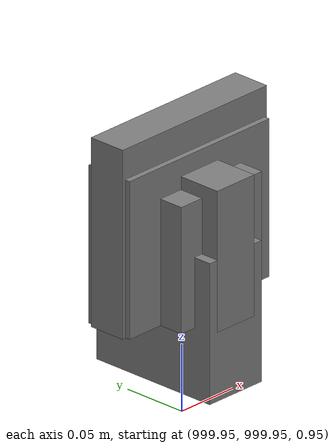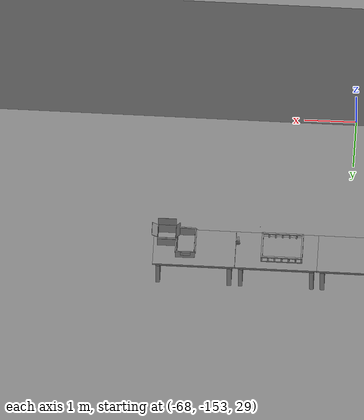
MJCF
<mujoco>
    <option gravity="0.000000000 0.000000000 -9.810000420" timestep="0.0049999999" integrator="implicitfast" density="1.225" viscosity="1.8000001e-05" noslip_iterations="10" iterations="100" sdf_iterations="50">
        <flag multiccd="disable"/>
    </option>
    <size memory="1000M"/>
    <compiler coordinate="local"/>
    <worldbody>
        <light cutoff="30" pos="0 1 1" dir="0 -1 -2"/>
        <light cutoff="30" pos="0 -1 1" dir="0 1 -2"/>
        <body pos="1000.000000000 1000.000000000 1.000000000" euler="0.000000000 0.000000000 180.000000000" name="openloong_gripper_2f85_fix_base_usda_wifi_box">
            <geom contype="1" conaffinity="1" density="1000" type="box" material="" rgba="0.500000000 0.500000000 0.500000000 1.000000000" solimp="0.899999976 0.949999988 0.001000000" friction="1.000000000 0.005000000 0.000100000" solref="0.020000000 1.000000000" margin="0" condim="3" group="0" pos="0.000000000 0.000000000 0.058978677" quat="0.000000000 0.000000047 0.000000000 1.000000000" size="0.068499997 0.018999999 0.059000000" name="openloong_gripper_2f85_fix_base_usda_geom_D9F07FE1_7A9D_49CA_86F1_C4800404654F"/>
            <freejoint name="openloong_gripper_2f85_fix_base_usda_wifi_box_joint"/>
            <site size="0.005000000 0.005000000 0.005000000" rgba="0.500000000 0.500000000 0.500000000 1.000000000" pos="0.000000000 0.000000000 0.000000000" quat="0.999961913 0.008726500 0.000000000 0.000000000" group="0" type="sphere" name="openloong_gripper_2f85_fix_base_usda_wifi_boxsite"/>
        </body>
        <body pos="1000.000000000 999.999938965 1.000000000" euler="0.000000000 0.000000000 180.000000000" name="openloong_gripper_2f85_fix_base_usda_intelcore_i5">
            <geom contype="1" conaffinity="1" density="1000" type="box" material="" rgba="0.500000000 0.500000000 0.500000000 1.000000000" solimp="0.899999976 0.949999988 0.001000000" friction="1.000000000 0.005000000 0.000100000" solref="0.020000000 1.000000000" margin="0" condim="3" group="0" pos="0.000000000 0.000000000 0.051722717" quat="0.707106709 0.000000000 0.000000000 -0.707106769" size="0.052800000 0.018080002 0.052800000" name="openloong_gripper_2f85_fix_base_usda_geom_1951ADB1_1A63_42E6_9360_A57FD798C2C9"/>
            <freejoint name="openloong_gripper_2f85_fix_base_usda_intelcore_i5_joint"/>
            <site size="0.005000000 0.005000000 0.005000000" rgba="0.500000000 0.500000000 0.500000000 1.000000000" pos="0.000000000 0.000000000 0.000000000" quat="0.999961913 0.008726534 0.000000000 0.000000000" group="0" type="sphere" name="openloong_gripper_2f85_fix_base_usda_intelcore_i5site"/>
        </body>
        <body pos="-65.814842224 -148.976974487 31.169977188" euler="68.959533691 83.758117676 156.663742065" mocap="true" name="spotlight6_SpotLight"/>
        <body pos="1000.000000000 1000.000000000 1.000000000" euler="0.000000000 0.000000000 180.000000000" name="openloong_gripper_2f85_fix_base_usda_cpu_fan">
            <geom contype="1" conaffinity="1" density="1000" type="box" material="" rgba="0.500000000 0.500000000 0.500000000 1.000000000" solimp="0.899999976 0.949999988 0.001000000" friction="1.000000000 0.005000000 0.000100000" solref="0.020000000 1.000000000" margin="0" condim="3" group="0" pos="0.000000000 0.000000000 0.070034981" quat="0.000000000 0.000000000 0.000000000 1.000000000" size="0.070700005 0.014699999 0.070700005" name="openloong_gripper_2f85_fix_base_usda_geom_9DFD10FF_371C_404C_B88C_6B6F04137D08"/>
            <freejoint name="openloong_gripper_2f85_fix_base_usda_cpu_fan_joint"/>
            <site size="0.005000000 0.005000000 0.005000000" rgba="0.500000000 0.500000000 0.500000000 1.000000000" pos="0.000000000 0.000000000 0.000000000" quat="0.999961913 0.008726535 0.000000000 0.000000000" group="0" type="sphere" name="openloong_gripper_2f85_fix_base_usda_cpu_fancsite"/>
        </body>
        <body pos="1000.000000000 1000.000000000 1.000000000" euler="0.000011953 0.000005123 -179.999984741" name="openloong_gripper_2f85_fix_base_usda_intel_box">
            <geom contype="1" conaffinity="1" density="1000" type="box" material="" rgba="0.500000000 0.500000000 0.500000000 1.000000000" solimp="0.899999976 0.949999988 0.001000000" friction="1.000000000 0.005000000 0.000100000" solref="0.020000000 1.000000000" margin="0" condim="3" group="0" pos="0.000000000 -0.000067139 0.000082284" quat="0.707106709 0.000000225 0.000000253 0.707106650" size="0.052800003 0.025300000 0.052800003" name="openloong_gripper_2f85_fix_base_usda_geom_CCDDD2CB_0F43_4509_A8D1_BF7DDDFAF182"/>
            <freejoint name="openloong_gripper_2f85_fix_base_usda_intel_box_joint"/>
            <site size="0.005000000 0.005000000 0.005000000" rgba="0.500000000 0.500000000 0.500000000 1.000000000" pos="0.000000000 0.000000000 0.000000000" quat="0.999961913 0.008726500 0.000000000 0.000000000" group="0" type="sphere" name="openloong_gripper_2f85_fix_base_usda_intel_boxsite"/>
        </body>
        <body pos="-66.367790222 -148.869918823 31.167709351" euler="110.570999146 -71.526626587 5.919467449" mocap="true" name="spotlight2_SpotLight"/>
        <body pos="-66.181030273 -149.685409546 31.170160294" euler="-146.413177490 6.804778576 21.384397507" mocap="true" name="spotlight3_SpotLight"/>
        <body pos="1000.000000000 1000.000000000 1.000000000" euler="0.000000000 0.000000000 180.000000000" name="openloong_gripper_2f85_fix_base_usda_battery_01">
            <geom contype="1" conaffinity="1" density="1000" type="box" material="" rgba="0.500000000 0.500000000 0.500000000 1.000000000" solimp="0.899999976 0.949999988 0.001000000" friction="1.000000000 0.005000000 0.000100000" solref="0.020000000 1.000000000" margin="0" condim="3" group="0" pos="-0.011123657 -0.041940309 0.101691343" quat="1.000000000 0.000000000 0.000000000 0.000000000" size="0.010800000 0.003375000 0.004725000" name="openloong_gripper_2f85_fix_base_usda_geom_3FDF966B_B73D_4F41_8651_DDD4E8AC009E"/>
            <geom contype="1" conaffinity="1" density="1000" type="box" material="" rgba="0.500000000 0.500000000 0.500000000 1.000000000" solimp="0.899999976 0.949999988 0.001000000" friction="1.000000000 0.005000000 0.000100000" solref="0.020000000 1.000000000" margin="0" condim="3" group="0" pos="-0.010876465 -0.044247437 0.047066893" quat="0.998702705 -0.050920475 0.000000000 0.000000000" size="0.009450001 0.002700000 0.024975000" name="openloong_gripper_2f85_fix_base_usda_geom_E69F7A0D_993B_4A60_8984_6608967FA8FC"/>
            <geom contype="1" conaffinity="1" density="1000" type="box" material="" rgba="0.500000000 0.500000000 0.500000000 1.000000000" solimp="0.899999976 0.949999988 0.001000000" friction="1.000000000 0.005000000 0.000100000" solref="0.020000000 1.000000000" margin="0" condim="3" group="0" pos="-0.001235962 -0.000659180 0.047381196" quat="1.000000000 0.000000000 0.000000000 0.000000000" size="0.039420001 0.039150000 0.047250003" name="openloong_gripper_2f85_fix_base_usda_geom_24D84B36_F279_47A7_9140_F0BC8F987959"/>
            <geom contype="1" conaffinity="1" density="1000" type="box" material="" rgba="0.500000000 0.500000000 0.500000000 1.000000000" solimp="0.899999976 0.949999988 0.001000000" friction="1.000000000 0.005000000 0.000100000" solref="0.020000000 1.000000000" margin="0" condim="3" group="0" pos="-0.010876465 -0.039138794 0.009851727" quat="1.000000000 0.000000000 0.000000000 0.000000000" size="0.009450001 0.010800000 0.013500000" name="openloong_gripper_2f85_fix_base_usda_geom_193D0A51_FB63_4541_97DD_A41F1FABB146"/>
            <geom contype="1" conaffinity="1" density="1000" type="box" material="" rgba="0.500000000 0.500000000 0.500000000 1.000000000" solimp="0.899999976 0.949999988 0.001000000" friction="1.000000000 0.005000000 0.000100000" solref="0.020000000 1.000000000" margin="0" condim="3" group="0" pos="-0.010876465 -0.041528322 0.071508206" quat="1.000000000 0.000000000 0.000000000 0.000000000" size="0.009450001 0.002700000 0.027000001" name="openloong_gripper_2f85_fix_base_usda_geom_E988394D_02B8_43CD_AAB2_2A5C6DC7483C"/>
            <freejoint name="openloong_gripper_2f85_fix_base_usda_battery_01_joint"/>
            <site size="0.005000000 0.005000000 0.005000000" rgba="0.500000000 0.500000000 0.500000000 1.000000000" pos="0.000000000 0.000000000 0.000000000" quat="0.999961913 0.008726500 0.000000000 0.000000000" group="0" type="sphere" name="openloong_gripper_2f85_fix_base_usda_battery_01site"/>
        </body>
        <body pos="-64.866622925 -149.383972168 30.183746338" euler="89.999984741 89.999946594 0.000000000" name="openloong_gripper_2f85_fix_base_usda_bluebox_01">
            <geom contype="1" conaffinity="1" density="1000" type="box" material="" rgba="0.500000000 0.500000000 0.500000000 1.000000000" solimp="0.899999976 0.949999988 0.001000000" friction="1.000000000 0.005000000 0.000100000" solref="0.020000000 1.000000000" margin="0" condim="3" group="0" pos="0.276580811 0.187225342 0.000068665" quat="0.707106948 0.000077471 0.707106352 0.000077486" size="0.100000001 0.057999998 0.010000000" name="openloong_gripper_2f85_fix_base_usda_geom_E0EC0B5D_19B7_4E9A_B343_514D0D734ADB"/>
            <geom contype="1" conaffinity="1" density="1000" type="box" material="" rgba="0.500000000 0.500000000 0.500000000 1.000000000" solimp="0.899999976 0.949999988 0.001000000" friction="1.000000000 0.005000000 0.000100000" solref="0.020000000 1.000000000" margin="0" condim="3" group="0" pos="0.000000000 0.002883911 0.000000000" quat="0.999999881 0.000000000 0.000000000 0.000000000" size="0.254000008 0.003000000 0.172000006" name="openloong_gripper_2f85_fix_base_usda_geom_02F1E21C_7846_4E1F_BC3F_368442608AD1"/>
            <geom contype="1" conaffinity="1" density="1000" type="box" material="" rgba="0.500000000 0.500000000 0.500000000 1.000000000" solimp="0.899999976 0.949999988 0.001000000" friction="1.000000000 0.005000000 0.000100000" solref="0.020000000 1.000000000" margin="0" condim="3" group="0" pos="0.000000000 0.124874115 0.173484802" quat="0.999796331 0.020176515 -0.000000015 0.000000030" size="0.259999990 0.119999997 0.007000000" name="openloong_gripper_2f85_fix_base_usda_geom_286FC39B_E0D8_445A_9467_D6A124CC2384"/>
            <geom contype="1" conaffinity="1" density="1000" type="box" material="" rgba="0.500000000 0.500000000 0.500000000 1.000000000" solimp="0.899999976 0.949999988 0.001000000" friction="1.000000000 0.005000000 0.000100000" solref="0.020000000 1.000000000" margin="0" condim="3" group="0" pos="0.000000000 0.124874115 -0.173469543" quat="0.999796331 -0.020176545 -0.000000015 0.000000000" size="0.259999990 0.119999997 0.007000000" name="openloong_gripper_2f85_fix_base_usda_geom_F3BF0630_2340_4438_8213_43949C6CE1DE"/>
            <geom contype="1" conaffinity="1" density="1000" type="box" material="" rgba="0.500000000 0.500000000 0.500000000 1.000000000" solimp="0.899999976 0.949999988 0.001000000" friction="1.000000000 0.005000000 0.000100000" solref="0.020000000 1.000000000" margin="0" condim="3" group="0" pos="0.000000000 0.214008331 0.188980103" quat="0.999912977 0.013176724 0.000000015 0.000000000" size="0.259999990 0.029999999 0.012500000" name="openloong_gripper_2f85_fix_base_usda_geom_8F23EDDB_9780_4F3D_A422_091D472A33E9"/>
            <geom contype="1" conaffinity="1" density="1000" type="box" material="" rgba="0.500000000 0.500000000 0.500000000 1.000000000" solimp="0.899999976 0.949999988 0.001000000" friction="1.000000000 0.005000000 0.000100000" solref="0.020000000 1.000000000" margin="0" condim="3" group="0" pos="-0.258361816 0.125289917 0.001876831" quat="0.702796936 -0.020792112 0.710783124 0.020769298" size="0.189999998 0.119999997 0.009000000" name="openloong_gripper_2f85_fix_base_usda_geom_FCE70157_0C29_4667_8BD5_A2AD6B34739E"/>
            <geom contype="1" conaffinity="1" density="1000" type="box" material="" rgba="0.500000000 0.500000000 0.500000000 1.000000000" solimp="0.899999976 0.949999988 0.001000000" friction="1.000000000 0.005000000 0.000100000" solref="0.020000000 1.000000000" margin="0" condim="3" group="0" pos="0.000000000 0.214008331 -0.188980103" quat="0.999912977 -0.013176769 0.000000030 0.000000015" size="0.259999990 0.029999999 0.012500000" name="openloong_gripper_2f85_fix_base_usda_geom_EB08C855_4FCA_4C35_9746_C00874EFBFCD"/>
            <geom contype="1" conaffinity="1" density="1000" type="box" material="" rgba="0.500000000 0.500000000 0.500000000 1.000000000" solimp="0.899999976 0.949999988 0.001000000" friction="1.000000000 0.005000000 0.000100000" solref="0.020000000 1.000000000" margin="0" condim="3" group="0" pos="-0.276611328 0.187225342 0.000068665" quat="0.707106650 0.000077441 0.707106709 0.000077456" size="0.100000001 0.057999998 0.010000000" name="openloong_gripper_2f85_fix_base_usda_geom_8A30C58B_C838_4352_9C89_9F34495A3D4F"/>
            <geom contype="1" conaffinity="1" density="1000" type="box" material="" rgba="0.500000000 0.500000000 0.500000000 1.000000000" solimp="0.899999976 0.949999988 0.001000000" friction="1.000000000 0.005000000 0.000100000" solref="0.020000000 1.000000000" margin="0" condim="3" group="0" pos="0.258331299 0.125289917 0.001876831" quat="0.702851415 0.018856421 0.710823774 -0.019329369" size="0.189999998 0.119999997 0.009000000" name="openloong_gripper_2f85_fix_base_usda_geom_BDD67C0A_99F9_4710_A904_FEBF34D2F4C9"/>
            <freejoint name="openloong_gripper_2f85_fix_base_usda_bluebox_01_joint"/>
            <site size="0.005000000 0.005000000 0.005000000" rgba="0.500000000 0.500000000 0.500000000 1.000000000" pos="0.000000000 0.000000000 0.000000000" quat="0.999961913 0.008726534 0.000000000 0.000000000" group="0" type="sphere" name="openloong_gripper_2f85_fix_base_usda_bluebox_01site"/>
        </body>
        <body pos="-64.496299744 -149.491867065 30.235729218" euler="0.000000000 0.000000000 89.999946594" name="openloong_gripper_2f85_fix_base_usda_cardboardbox_01">
            <geom contype="1" conaffinity="1" density="1000" type="box" material="" rgba="0.500000000 0.500000000 0.500000000 1.000000000" solimp="0.899999976 0.949999988 0.001000000" friction="1.000000000 0.005000000 0.000100000" solref="0.020000000 1.000000000" margin="0" condim="3" group="0" pos="-0.003166199 -0.004086494 0.005052090" quat="1.000000000 0.000000000 0.000000000 0.000000000" size="0.142499998 0.177500010 0.005000000" name="openloong_gripper_2f85_fix_base_usda_geom_C81458D2_611C_47A5_993E_5888B64F3DCF"/>
            <geom contype="1" conaffinity="1" density="1000" type="box" material="" rgba="0.500000000 0.500000000 0.500000000 1.000000000" solimp="0.899999976 0.949999988 0.001000000" friction="1.000000000 0.005000000 0.000100000" solref="0.020000000 1.000000000" margin="0" condim="3" group="0" pos="-0.003166199 0.170316696 0.150570869" quat="1.000000000 0.000000000 0.000000000 0.000000000" size="0.142499998 0.005000000 0.149999991" name="openloong_gripper_2f85_fix_base_usda_geom_E4F3543A_CC4E_4C9D_8852_BBEAFF169775"/>
            <geom contype="1" conaffinity="1" density="1000" type="box" material="" rgba="0.500000000 0.500000000 0.500000000 1.000000000" solimp="0.899999976 0.949999988 0.001000000" friction="1.000000000 0.005000000 0.000100000" solref="0.020000000 1.000000000" margin="0" condim="3" group="0" pos="-0.147399902 -0.005307198 0.150570869" quat="1.000000000 0.000000000 0.000000000 0.000000000" size="0.005000000 0.177500010 0.149999991" name="openloong_gripper_2f85_fix_base_usda_geom_97F5D0F5_EE64_44CF_B4CC_E3627B811F2C"/>
            <geom contype="1" conaffinity="1" density="1000" type="box" material="" rgba="0.500000000 0.500000000 0.500000000 1.000000000" solimp="0.899999976 0.949999988 0.001000000" friction="1.000000000 0.005000000 0.000100000" solref="0.020000000 1.000000000" margin="0" condim="3" group="0" pos="0.140275955 -0.005307198 0.150570869" quat="1.000000000 0.000000000 0.000000000 0.000000000" size="0.005000000 0.177500010 0.149999991" name="openloong_gripper_2f85_fix_base_usda_geom_61AD66E6_56D1_48AD_BFFD_762A81A2F533"/>
            <geom contype="1" conaffinity="1" density="1000" type="box" material="" rgba="0.500000000 0.500000000 0.500000000 1.000000000" solimp="0.899999976 0.949999988 0.001000000" friction="1.000000000 0.005000000 0.000100000" solref="0.020000000 1.000000000" margin="0" condim="3" group="0" pos="-0.003166199 -0.181550980 0.150570869" quat="1.000000000 0.000000000 0.000000000 0.000000000" size="0.142499998 0.005000000 0.149999991" name="openloong_gripper_2f85_fix_base_usda_geom_ABAA5209_54FE_4FCA_B2C4_5026ED374287"/>
            <freejoint name="openloong_gripper_2f85_fix_base_usda_cardboardbox_01_joint"/>
            <site size="0.005000000 0.005000000 0.005000000" rgba="0.500000000 0.500000000 0.500000000 1.000000000" pos="0.000000000 0.000000000 0.000000000" quat="0.999961913 0.008726535 0.000000000 0.000000000" group="0" type="sphere" name="openloong_gripper_2f85_fix_base_usda_site_246DD8E3_A9F9_4267_9FB3_94399118F428"/>
            <body pos="0.139160156 -0.004048347 0.301930904" euler="-179.999954224 49.383502960 179.999954224" name="openloong_gripper_2f85_fix_base_usda_A1_006">
                <geom contype="1" conaffinity="1" density="1000" type="box" material="" rgba="0.500000000 0.500000000 0.500000000 1.000000000" solimp="0.899999976 0.949999988 0.001000000" friction="1.000000000 0.005000000 0.000100000" solref="0.020000000 1.000000000" margin="0" condim="3" group="0" pos="-0.071587563 0.000009537 0.001745224" quat="0.999999881 0.000000000 0.000000000 0.000000000" size="0.071249999 0.179999992 0.002500000" name="openloong_gripper_2f85_fix_base_usda_geom_AA320538_32DA_4B99_A247_72C7E56A0427"/>
                <joint armature="0" stiffness="0.07" damping="0.0099999998" axis="0.000000 1.000000 0.000000" type="hinge" name="openloong_gripper_2f85_fix_base_usda_A1_006"/>
            </body>
            <body pos="-0.145902634 -0.004086494 0.301938057" euler="-180.000000000 -60.000011444 -180.000000000" name="openloong_gripper_2f85_fix_base_usda_A2_006">
                <geom contype="1" conaffinity="1" density="1000" type="box" material="" rgba="0.500000000 0.500000000 0.500000000 1.000000000" solimp="0.899999976 0.949999988 0.001000000" friction="1.000000000 0.005000000 0.000100000" solref="0.020000000 1.000000000" margin="0" condim="3" group="0" pos="0.071268082 0.000009537 0.002717972" quat="0.000002921 0.000000000 -0.000000030 0.999999881" size="0.071249999 0.179999992 0.002500000" name="openloong_gripper_2f85_fix_base_usda_geom_57556E6B_FA2B_4B23_9EC1_73F34E211F15"/>
                <joint armature="0" stiffness="0.07" damping="0.0099999998" axis="0.000000 1.000000 0.000000" type="hinge" name="openloong_gripper_2f85_fix_base_usda_A2_006"/>
            </body>
            <body pos="-0.003385544 0.175991058 0.301930904" euler="-125.858116150 -0.000004561 0.000002331" name="openloong_gripper_2f85_fix_base_usda_B2_006">
                <geom contype="1" conaffinity="1" density="1000" type="box" material="" rgba="0.500000000 0.500000000 0.500000000 1.000000000" solimp="0.899999976 0.949999988 0.001000000" friction="1.000000000 0.005000000 0.000100000" solref="0.020000000 1.000000000" margin="0" condim="3" group="0" pos="0.000009537 -0.070939064 -0.002470016" quat="0.999614120 0.027776197 -0.000000015 0.000000030" size="0.137500003 0.064999998 0.005000000" name="openloong_gripper_2f85_fix_base_usda_geom_3280D6FE_129C_4DCF_88E7_3B9ADE1FBDBF"/>
                <joint armature="0" stiffness="0.07" damping="0.0099999998" axis="1.000000 0.000000 0.000000" type="hinge" name="openloong_gripper_2f85_fix_base_usda_B2_006"/>
            </body>
            <body pos="-0.003385544 -0.184140205 0.301938057" euler="147.805557251 0.000000000 0.000000000" name="openloong_gripper_2f85_fix_base_usda_B1_006">
                <geom contype="1" conaffinity="1" density="1000" type="box" material="" rgba="0.500000000 0.500000000 0.500000000 1.000000000" solimp="0.899999976 0.949999988 0.001000000" friction="1.000000000 0.005000000 0.000100000" solref="0.020000000 1.000000000" margin="0" condim="3" group="0" pos="-0.000028610 0.070202351 -0.002703667" quat="0.999614179 -0.027776167 0.000000000 0.000000000" size="0.137500003 0.064999998 0.005000000" name="openloong_gripper_2f85_fix_base_usda_geom_D983586D_1060_4E06_AEEC_FD199AE4566A"/>
                <joint armature="0" stiffness="0.07" damping="0.0099999998" axis="1.000000 0.000000 0.000000" type="hinge" name="openloong_gripper_2f85_fix_base_usda_B1_006"/>
            </body>
        </body>
        <body pos="-65.882858276 -149.481979370 30.229999542" euler="-64.487716675 0.000000000 0.000000000" name="openloong_gripper_2f85_fix_base_usda_Barcode">
            <geom contype="1" conaffinity="1" density="1000" type="box" material="" rgba="0.500000000 0.500000000 0.500000000 1.000000000" solimp="0.899999976 0.949999988 0.001000000" friction="1.000000000 0.005000000 0.000100000" solref="0.020000000 1.000000000" margin="0" condim="3" group="0" pos="0.000000000 0.013038635 0.001419067" quat="0.000000000 0.000000000 0.000000000 1.000000119" size="0.034000002 0.010000000 0.017999999" name="openloong_gripper_2f85_fix_base_usda_geom_E2DED5B3_9843_4CD3_8CAC_E3BE42978D9D"/>
            <geom contype="1" conaffinity="1" density="1000" type="box" material="" rgba="0.500000000 0.500000000 0.500000000 1.000000000" solimp="0.899999976 0.949999988 0.001000000" friction="1.000000000 0.005000000 0.000100000" solref="0.020000000 1.000000000" margin="0" condim="3" group="0" pos="0.000000000 -0.035301208 -0.007095337" quat="0.000000000 0.000000000 -0.043619365 0.999048233" size="0.028999999 0.010000000 0.020000000" name="openloong_gripper_2f85_fix_base_usda_geom_89846C0F_2324_4A03_A4D1_64ED45E5C04E"/>
            <geom contype="1" conaffinity="1" density="1000" type="box" material="" rgba="0.500000000 0.500000000 0.500000000 1.000000000" solimp="0.899999976 0.949999988 0.001000000" friction="1.000000000 0.005000000 0.000100000" solref="0.020000000 1.000000000" margin="0" condim="3" group="0" pos="0.000000000 -0.043411255 -0.011749268" quat="0.922262907 0.386563420 0.000000000 0.000000000" size="0.026000001 0.010000000 0.020000000" name="openloong_gripper_2f85_fix_base_usda_geom_03C3CC80_6E46_4319_AA97_F88DC4670472"/>
            <geom contype="1" conaffinity="1" density="1000" type="box" material="" rgba="0.500000000 0.500000000 0.500000000 1.000000000" solimp="0.899999976 0.949999988 0.001000000" friction="1.000000000 0.005000000 0.000100000" solref="0.020000000 1.000000000" margin="0" condim="3" group="0" pos="0.000000000 -0.016967773 -0.031860352" quat="0.000000000 0.000000000 0.000000000 1.000000119" size="0.008000000 0.010000000 0.013000000" name="openloong_gripper_2f85_fix_base_usda_geom_9A76BDBD_2BF4_480F_BC71_64A66B51B485"/>
            <geom contype="1" conaffinity="1" density="1000" type="box" material="" rgba="0.500000000 0.500000000 0.500000000 1.000000000" solimp="0.899999976 0.949999988 0.001000000" friction="1.000000000 0.005000000 0.000100000" solref="0.020000000 1.000000000" margin="0" condim="3" group="0" pos="0.000000000 -0.001869202 0.000312805" quat="0.953716993 0.300705761 0.000000000 0.000000000" size="0.032000002 0.010000000 0.018999999" name="openloong_gripper_2f85_fix_base_usda_geom_D343664D_F888_4C53_91F0_898D085F9EB8"/>
            <geom contype="1" conaffinity="1" density="1000" type="box" material="" rgba="0.500000000 0.500000000 0.500000000 1.000000000" solimp="0.899999976 0.949999988 0.001000000" friction="1.000000000 0.005000000 0.000100000" solref="0.020000000 1.000000000" margin="0" condim="3" group="0" pos="0.000000000 -0.019531250 -0.003173828" quat="0.953716993 0.300705761 0.000000000 0.000000000" size="0.030999999 0.010000000 0.020000000" name="openloong_gripper_2f85_fix_base_usda_geom_0F8F1C17_1BCC_4860_974C_43B7D5677F7C"/>
            <geom contype="1" conaffinity="1" density="1000" type="box" material="" rgba="0.500000000 0.500000000 0.500000000 1.000000000" solimp="0.899999976 0.949999988 0.001000000" friction="1.000000000 0.005000000 0.000100000" solref="0.020000000 1.000000000" margin="0" condim="3" group="0" pos="0.000000000 -0.035301208 -0.007095337" quat="0.953716993 0.300705761 0.000000000 0.000000000" size="0.028999999 0.010000000 0.020000000" name="openloong_gripper_2f85_fix_base_usda_geom_A40F488D_3FDA_4F84_82D8_EAE473B0E914"/>
            <geom contype="1" conaffinity="1" density="1000" type="box" material="" rgba="0.500000000 0.500000000 0.500000000 1.000000000" solimp="0.899999976 0.949999988 0.001000000" friction="1.000000000 0.005000000 0.000100000" solref="0.020000000 1.000000000" margin="0" condim="3" group="0" pos="0.000000000 -0.042617798 -0.071121216" quat="0.000000000 0.000000000 0.000000000 1.000000119" size="0.013000000 0.021000000 0.059999999" name="openloong_gripper_2f85_fix_base_usda_geom_039E58B6_8A51_46BB_AE82_643A4FC9B47D"/>
            <freejoint name="openloong_gripper_2f85_fix_base_usda_Barcode_joint"/>
            <site size="0.005000000 0.005000000 0.005000000" rgba="0.500000000 0.500000000 0.500000000 1.000000000" pos="0.000000000 0.000000000 0.000000000" quat="1.000000000 0.000000000 0.000000000 0.000000000" group="0" type="sphere" name="openloong_gripper_2f85_fix_base_usda_Barcode_site"/>
        </body>
        <body pos="-66.745018005 -149.392349243 30.184000015" euler="0.000000000 0.000000000 89.999946594" name="[22332184433200]_Basket_01">
            <geom contype="1" conaffinity="1" density="1000" type="box" material="" rgba="0.500000000 0.500000000 0.500000000 1.000000000" solimp="0.899999976 0.949999988 0.001000000" friction="1.000000000 0.005000000 0.000100000" solref="0.020000000 1.000000000" margin="0" condim="3" group="0" pos="-0.052425385 0.389207840 0.089787483" quat="0.707107008 0.000000000 0.000000000 0.707106411" size="0.014249999 0.014249999 0.059999999" name="[22332184433200]_geom_57105DD3_4D86_4B82_AF20_E2F5D3D279A0"/>
            <geom contype="1" conaffinity="1" density="1000" type="box" material="" rgba="0.500000000 0.500000000 0.500000000 1.000000000" solimp="0.899999976 0.949999988 0.001000000" friction="1.000000000 0.005000000 0.000100000" solref="0.020000000 1.000000000" margin="0" condim="3" group="0" pos="0.264015198 -0.133043289 0.089787483" quat="0.707107008 0.000000000 0.000000000 0.707106411" size="0.014249999 0.014249999 0.059999999" name="[22332184433200]_geom_C0716535_8ED5_4376_848D_9AED2E6D705C"/>
            <geom contype="1" conaffinity="1" density="1000" type="box" material="" rgba="0.500000000 0.500000000 0.500000000 1.000000000" solimp="0.899999976 0.949999988 0.001000000" friction="1.000000000 0.005000000 0.000100000" solref="0.020000000 1.000000000" margin="0" condim="3" group="0" pos="-0.264015198 -0.265548706 0.089793205" quat="0.707107008 0.000000000 0.000000000 0.707106411" size="0.014249999 0.014249999 0.059999999" name="[22332184433200]_geom_87CB13AF_E418_48C9_B184_9DCB111B797E"/>
            <geom contype="1" conaffinity="1" density="1000" type="box" material="" rgba="0.500000000 0.500000000 0.500000000 1.000000000" solimp="0.899999976 0.949999988 0.001000000" friction="1.000000000 0.005000000 0.000100000" solref="0.020000000 1.000000000" margin="0" condim="3" group="0" pos="-0.160263062 -0.389322281 0.089793205" quat="0.707107008 0.000000000 0.000000000 0.707106411" size="0.014249999 0.014249999 0.059999999" name="[22332184433200]_geom_9ED9A7A7_9A3E_4EBF_B552_C1442B919228"/>
            <geom contype="1" conaffinity="1" density="1000" type="box" material="" rgba="0.500000000 0.500000000 0.500000000 1.000000000" solimp="0.899999976 0.949999988 0.001000000" friction="1.000000000 0.005000000 0.000100000" solref="0.020000000 1.000000000" margin="0" condim="3" group="0" pos="0.162265778 -0.389322281 0.089787483" quat="0.707107008 0.000000000 0.000000000 0.707106411" size="0.014249999 0.014249999 0.059999999" name="[22332184433200]_geom_7778DD52_1632_40E9_B416_DB9221811AA3"/>
            <geom contype="1" conaffinity="1" density="1000" type="box" material="" rgba="0.500000000 0.500000000 0.500000000 1.000000000" solimp="0.899999976 0.949999988 0.001000000" friction="1.000000000 0.005000000 0.000100000" solref="0.020000000 1.000000000" margin="0" condim="3" group="0" pos="0.264015198 0.389207840 0.089787483" quat="0.707107008 0.000000000 0.000000000 0.707106411" size="0.014249999 0.014249999 0.059999999" name="[22332184433200]_geom_103CCC91_3A51_494D_A109_B8565EAB0369"/>
            <geom contype="1" conaffinity="1" density="1000" type="box" material="" rgba="0.500000000 0.500000000 0.500000000 1.000000000" solimp="0.899999976 0.949999988 0.001000000" friction="1.000000000 0.005000000 0.000100000" solref="0.020000000 1.000000000" margin="0" condim="3" group="0" pos="-0.264015198 -0.133043289 0.089793205" quat="0.707107008 0.000000000 0.000000000 0.707106411" size="0.014249999 0.014249999 0.059999999" name="[22332184433200]_geom_5E83BC90_3FC8_4728_9B26_7DFE232A7312"/>
            <geom contype="1" conaffinity="1" density="1000" type="box" material="" rgba="0.500000000 0.500000000 0.500000000 1.000000000" solimp="0.899999976 0.949999988 0.001000000" friction="1.000000000 0.005000000 0.000100000" solref="0.020000000 1.000000000" margin="0" condim="3" group="0" pos="-0.264026642 0.269256592 0.089793205" quat="0.707107008 0.000000000 0.000000000 0.707106411" size="0.014249999 0.014249999 0.059999999" name="[22332184433200]_geom_484909C4_4B9E_4C06_B0F4_801A3AB0FE26"/>
            <geom contype="1" conaffinity="1" density="1000" type="box" material="" rgba="0.500000000 0.500000000 0.500000000 1.000000000" solimp="0.899999976 0.949999988 0.001000000" friction="1.000000000 0.005000000 0.000100000" solref="0.020000000 1.000000000" margin="0" condim="3" group="0" pos="0.054462433 0.389207840 0.089787483" quat="0.707107008 0.000000000 0.000000000 0.707106411" size="0.014249999 0.014249999 0.059999999" name="[22332184433200]_geom_3A073938_7616_4DF8_84DC_818EF93542F2"/>
            <geom contype="1" conaffinity="1" density="1000" type="box" material="" rgba="0.500000000 0.500000000 0.500000000 1.000000000" solimp="0.899999976 0.949999988 0.001000000" friction="1.000000000 0.005000000 0.000100000" solref="0.020000000 1.000000000" margin="0" condim="3" group="0" pos="0.054462433 -0.389322281 0.089787483" quat="0.707107008 0.000000000 0.000000000 0.707106411" size="0.014249999 0.014249999 0.059999999" name="[22332184433200]_geom_15DE845A_8EB7_4C0C_AA9F_B4EC8D1DE479"/>
            <geom contype="1" conaffinity="1" density="1000" type="box" material="" rgba="0.500000000 0.500000000 0.500000000 1.000000000" solimp="0.899999976 0.949999988 0.001000000" friction="1.000000000 0.005000000 0.000100000" solref="0.020000000 1.000000000" margin="0" condim="3" group="0" pos="0.264015198 0.269256592 0.089793205" quat="0.707107008 0.000000000 0.000000000 0.707106411" size="0.014249999 0.014249999 0.059999999" name="[22332184433200]_geom_8CFB049C_2563_43BF_B035_2692B0EC95E4"/>
            <geom contype="1" conaffinity="1" density="1000" type="box" material="" rgba="0.500000000 0.500000000 0.500000000 1.000000000" solimp="0.899999976 0.949999988 0.001000000" friction="1.000000000 0.005000000 0.000100000" solref="0.020000000 1.000000000" margin="0" condim="3" group="0" pos="0.264015198 -0.389322281 0.089787483" quat="0.707107008 0.000000000 0.000000000 0.707106411" size="0.014249999 0.014249999 0.059999999" name="[22332184433200]_geom_F64AEE4B_4EF9_4596_A854_10A76A99D2D7"/>
            <geom contype="1" conaffinity="1" density="1000" type="box" material="" rgba="0.500000000 0.500000000 0.500000000 1.000000000" solimp="0.899999976 0.949999988 0.001000000" friction="1.000000000 0.005000000 0.000100000" solref="0.020000000 1.000000000" margin="0" condim="3" group="0" pos="0.000000000 0.000000000 0.015998840" quat="0.707107008 0.000000000 0.000000000 0.707106411" size="0.403499991 0.279000014 0.015750000" name="[22332184433200]_geom_150397FC_59E0_4B6B_9C07_79483BD6DEAC"/>
            <geom contype="1" conaffinity="1" density="1000" type="box" material="" rgba="0.500000000 0.500000000 0.500000000 1.000000000" solimp="0.899999976 0.949999988 0.001000000" friction="1.000000000 0.005000000 0.000100000" solref="0.020000000 1.000000000" margin="0" condim="3" group="0" pos="0.000000000 -0.389476776 0.163619041" quat="0.707107008 0.000000000 0.000000000 0.707106411" size="0.015000000 0.277500004 0.015750000" name="[22332184433200]_geom_FF131390_4196_48FA_B9D7_E9BF50203D4F"/>
            <geom contype="1" conaffinity="1" density="1000" type="box" material="" rgba="0.500000000 0.500000000 0.500000000 1.000000000" solimp="0.899999976 0.949999988 0.001000000" friction="1.000000000 0.005000000 0.000100000" solref="0.020000000 1.000000000" margin="0" condim="3" group="0" pos="0.162265778 0.389207840 0.089787483" quat="0.707107008 0.000000000 0.000000000 0.707106411" size="0.014249999 0.014249999 0.059999999" name="[22332184433200]_geom_224E4096_4448_4769_BED9_08CFF0E176C3"/>
            <geom contype="1" conaffinity="1" density="1000" type="box" material="" rgba="0.500000000 0.500000000 0.500000000 1.000000000" solimp="0.899999976 0.949999988 0.001000000" friction="1.000000000 0.005000000 0.000100000" solref="0.020000000 1.000000000" margin="0" condim="3" group="0" pos="0.000000000 0.389471054 0.163619041" quat="0.707107008 0.000000000 0.000000000 0.707106411" size="0.015000000 0.277500004 0.015750000" name="[22332184433200]_geom_ABD66939_6D8F_437C_A250_1BAB3FC58917"/>
            <geom contype="1" conaffinity="1" density="1000" type="box" material="" rgba="0.500000000 0.500000000 0.500000000 1.000000000" solimp="0.899999976 0.949999988 0.001000000" friction="1.000000000 0.005000000 0.000100000" solref="0.020000000 1.000000000" margin="0" condim="3" group="0" pos="-0.263511658 0.000000000 0.163619041" quat="0.707107008 0.000000000 0.000000000 0.707106411" size="0.403499991 0.015000000 0.015750000" name="[22332184433200]_geom_D07AD2F0_B5FF_4EA9_99DB_F54ADFFB6796"/>
            <geom contype="1" conaffinity="1" density="1000" type="box" material="" rgba="0.500000000 0.500000000 0.500000000 1.000000000" solimp="0.899999976 0.949999988 0.001000000" friction="1.000000000 0.005000000 0.000100000" solref="0.020000000 1.000000000" margin="0" condim="3" group="0" pos="-0.264015198 0.141334534 0.089793205" quat="0.707107008 0.000000000 0.000000000 0.707106411" size="0.014249999 0.014249999 0.059999999" name="[22332184433200]_geom_F0BBF85C_FF75_4D0C_92C7_B0B16734502B"/>
            <geom contype="1" conaffinity="1" density="1000" type="box" material="" rgba="0.500000000 0.500000000 0.500000000 1.000000000" solimp="0.899999976 0.949999988 0.001000000" friction="1.000000000 0.005000000 0.000100000" solref="0.020000000 1.000000000" margin="0" condim="3" group="0" pos="0.264015198 -0.265548706 0.089787483" quat="0.707107008 0.000000000 0.000000000 0.707106411" size="0.014249999 0.014249999 0.059999999" name="[22332184433200]_geom_CB123FCC_57E0_483D_8C8F_DAEA7200BCFC"/>
            <geom contype="1" conaffinity="1" density="1000" type="box" material="" rgba="0.500000000 0.500000000 0.500000000 1.000000000" solimp="0.899999976 0.949999988 0.001000000" friction="1.000000000 0.005000000 0.000100000" solref="0.020000000 1.000000000" margin="0" condim="3" group="0" pos="-0.160263062 0.389207840 0.089787483" quat="0.707107008 0.000000000 0.000000000 0.707106411" size="0.014249999 0.014249999 0.059999999" name="[22332184433200]_geom_D5904246_1C41_4EF9_9100_776CAAD8F1F9"/>
            <geom contype="1" conaffinity="1" density="1000" type="box" material="" rgba="0.500000000 0.500000000 0.500000000 1.000000000" solimp="0.899999976 0.949999988 0.001000000" friction="1.000000000 0.005000000 0.000100000" solref="0.020000000 1.000000000" margin="0" condim="3" group="0" pos="-0.052425385 -0.389322281 0.089787483" quat="0.707107008 0.000000000 0.000000000 0.707106411" size="0.014249999 0.014249999 0.059999999" name="[22332184433200]_geom_C6FC06C9_89EA_48B6_81A9_086CCFA780CA"/>
            <geom contype="1" conaffinity="1" density="1000" type="box" material="" rgba="0.500000000 0.500000000 0.500000000 1.000000000" solimp="0.899999976 0.949999988 0.001000000" friction="1.000000000 0.005000000 0.000100000" solref="0.020000000 1.000000000" margin="0" condim="3" group="0" pos="-0.264026642 -0.389322281 0.089793205" quat="0.707107008 0.000000000 0.000000000 0.707106411" size="0.014249999 0.014249999 0.059999999" name="[22332184433200]_geom_E88ECB68_F597_4391_81B8_EB005038A4BC"/>
            <geom contype="1" conaffinity="1" density="1000" type="box" material="" rgba="0.500000000 0.500000000 0.500000000 1.000000000" solimp="0.899999976 0.949999988 0.001000000" friction="1.000000000 0.005000000 0.000100000" solref="0.020000000 1.000000000" margin="0" condim="3" group="0" pos="0.264015198 0.141334534 0.089787483" quat="0.707107008 0.000000000 0.000000000 0.707106411" size="0.014249999 0.014249999 0.059999999" name="[22332184433200]_geom_773B0664_0DC1_403A_9476_B566FC04B917"/>
            <geom contype="1" conaffinity="1" density="1000" type="box" material="" rgba="0.500000000 0.500000000 0.500000000 1.000000000" solimp="0.899999976 0.949999988 0.001000000" friction="1.000000000 0.005000000 0.000100000" solref="0.020000000 1.000000000" margin="0" condim="3" group="0" pos="-0.264015198 0.389207840 0.089793205" quat="0.707107008 0.000000000 0.000000000 0.707106411" size="0.014249999 0.014249999 0.059999999" name="[22332184433200]_geom_CCB6C647_E778_4529_BAC1_021ABCF46CDA"/>
            <geom contype="1" conaffinity="1" density="1000" type="box" material="" rgba="0.500000000 0.500000000 0.500000000 1.000000000" solimp="0.899999976 0.949999988 0.001000000" friction="1.000000000 0.005000000 0.000100000" solref="0.020000000 1.000000000" margin="0" condim="3" group="0" pos="0.264015198 0.004480362 0.089787483" quat="0.707107008 0.000000000 0.000000000 0.707106411" size="0.014249999 0.014249999 0.059999999" name="[22332184433200]_geom_1DCA2142_B023_4FB1_BA4D_5BC942667BB8"/>
            <geom contype="1" conaffinity="1" density="1000" type="box" material="" rgba="0.500000000 0.500000000 0.500000000 1.000000000" solimp="0.899999976 0.949999988 0.001000000" friction="1.000000000 0.005000000 0.000100000" solref="0.020000000 1.000000000" margin="0" condim="3" group="0" pos="0.263694763 -0.000011444 0.163619041" quat="0.707107008 0.000000000 0.000000000 0.707106411" size="0.403499991 0.015000000 0.015750000" name="[22332184433200]_geom_AB8A87C6_F0F1_4F28_94C1_6A1C70011A9B"/>
            <geom contype="1" conaffinity="1" density="1000" type="box" material="" rgba="0.500000000 0.500000000 0.500000000 1.000000000" solimp="0.899999976 0.949999988 0.001000000" friction="1.000000000 0.005000000 0.000100000" solref="0.020000000 1.000000000" margin="0" condim="3" group="0" pos="-0.264015198 0.004480362 0.089793205" quat="0.707107008 0.000000000 0.000000000 0.707106411" size="0.014249999 0.014249999 0.059999999" name="[22332184433200]_geom_75C63488_C6C2_4F7A_AE82_14511FFA9167"/>
            <freejoint name="[22332184433200]_joint_277297D4_532B_4B34_95F9_CCAA94AC70E2"/>
        </body>
        <body pos="0.000000000 0.000000000 0.000000000" euler="0.000000000 0.000000000 0.000000000" name="Static Objects_Static Objects">
            <geom contype="1" conaffinity="1" density="1000" type="box" material="" rgba="0.500000000 0.500000000 0.500000000 1.000000000" solimp="0.899999976 0.949999988 0.001000000" friction="1.000000000 0.005000000 0.000100000" solref="0.020000000 1.000000000" margin="0" condim="3" group="0" pos="-67.544113159 -149.365814209 29.727830887" quat="0.500000417 0.499999970 0.499999553 0.499999970" size="0.381000012 0.319999993 0.041000001" name="Static Objects_geom_BD9CDD47_6574_4130_B130_2C8636C9711C"/>
            <geom contype="1" conaffinity="1" density="1000" type="box" material="" rgba="0.500000000 0.500000000 0.500000000 1.000000000" solimp="0.899999976 0.949999988 0.001000000" friction="1.000000000 0.005000000 0.000100000" solref="0.020000000 1.000000000" margin="0" condim="3" group="0" pos="-68.239501953 -149.365814209 30.086868286" quat="0.500000417 0.499999970 0.499999553 0.499999970" size="0.370999992 0.039500002 0.745000005" name="Static Objects_geom_30521A7B_F2BD_42D0_B463_7579BED85321"/>
            <geom contype="1" conaffinity="1" density="1000" type="box" material="" rgba="0.500000000 0.500000000 0.500000000 1.000000000" solimp="0.899999976 0.949999988 0.001000000" friction="1.000000000 0.005000000 0.000100000" solref="0.020000000 1.000000000" margin="0" condim="3" group="0" pos="-68.239501953 -149.365814209 30.147235870" quat="0.500000417 0.499999970 0.499999553 0.499999970" size="0.400000006 0.022000000 0.800000012" name="Static Objects_geom_3E259749_35E5_4AE1_B6E1_6A15703E5956"/>
            <geom contype="1" conaffinity="1" density="1000" type="box" material="" rgba="0.500000000 0.500000000 0.500000000 1.000000000" solimp="0.899999976 0.949999988 0.001000000" friction="1.000000000 0.005000000 0.000100000" solref="0.020000000 1.000000000" margin="0" condim="3" group="0" pos="-68.934890747 -149.365814209 29.727830887" quat="0.500000417 0.499999970 0.499999553 0.499999970" size="0.381000012 0.319999993 0.041000001" name="Static Objects_geom_5F1CEB61_0B9D_45EC_B7EC_F71398A10CE7"/>
            <geom contype="1" conaffinity="1" density="1000" type="box" material="" rgba="0.500000000 0.500000000 0.500000000 1.000000000" solimp="0.899999976 0.949999988 0.001000000" friction="1.000000000 0.005000000 0.000100000" solref="0.020000000 1.000000000" margin="0" condim="3" group="0" pos="-68.239501953 -149.365814209 29.561563492" quat="0.500000417 0.499999970 0.499999553 0.499999970" size="0.020000000 0.022000000 0.660000026" name="Static Objects_geom_6BBA1D99_B55F_4E12_A16D_C779BB43E77F"/>
            <geom contype="1" conaffinity="1" density="1000" type="box" material="" rgba="0.500000000 0.500000000 0.500000000 1.000000000" solimp="0.899999976 0.949999988 0.001000000" friction="1.000000000 0.005000000 0.000100000" solref="0.020000000 1.000000000" margin="0" condim="3" group="0" pos="-65.945671082 -149.365814209 29.727830887" quat="0.500000417 0.499999970 0.499999553 0.499999970" size="0.381000012 0.319999993 0.041000001" name="Static Objects_geom_A98E76AE_01AE_4F2F_9E9A_436E804860D1"/>
            <geom contype="1" conaffinity="1" density="1000" type="box" material="" rgba="0.500000000 0.500000000 0.500000000 1.000000000" solimp="0.899999976 0.949999988 0.001000000" friction="1.000000000 0.005000000 0.000100000" solref="0.020000000 1.000000000" margin="0" condim="3" group="0" pos="-66.641059875 -149.365814209 30.086868286" quat="0.500000417 0.499999970 0.499999553 0.499999970" size="0.370999992 0.039500002 0.745000005" name="Static Objects_geom_127C4258_AFE7_418B_9E61_A3EDCAB1BDDC"/>
            <geom contype="1" conaffinity="1" density="1000" type="box" material="" rgba="0.500000000 0.500000000 0.500000000 1.000000000" solimp="0.899999976 0.949999988 0.001000000" friction="1.000000000 0.005000000 0.000100000" solref="0.020000000 1.000000000" margin="0" condim="3" group="0" pos="-66.641059875 -149.365814209 30.147235870" quat="0.500000417 0.499999970 0.499999553 0.499999970" size="0.400000006 0.022000000 0.800000012" name="Static Objects_geom_B00A063E_106E_4C8C_84DE_8C5A5E85D8F0"/>
            <geom contype="1" conaffinity="1" density="1000" type="box" material="" rgba="0.500000000 0.500000000 0.500000000 1.000000000" solimp="0.899999976 0.949999988 0.001000000" friction="1.000000000 0.005000000 0.000100000" solref="0.020000000 1.000000000" margin="0" condim="3" group="0" pos="-67.336448669 -149.365814209 29.727830887" quat="0.500000417 0.499999970 0.499999553 0.499999970" size="0.381000012 0.319999993 0.041000001" name="Static Objects_geom_78AC5BD2_5734_489D_B17C_BAB8D82D2AAD"/>
            <geom contype="1" conaffinity="1" density="1000" type="box" material="" rgba="0.500000000 0.500000000 0.500000000 1.000000000" solimp="0.899999976 0.949999988 0.001000000" friction="1.000000000 0.005000000 0.000100000" solref="0.020000000 1.000000000" margin="0" condim="3" group="0" pos="-66.641059875 -149.365814209 29.561563492" quat="0.500000417 0.499999970 0.499999553 0.499999970" size="0.020000000 0.022000000 0.660000026" name="Static Objects_geom_C1431217_8B0C_4101_8CC4_3697945FED0A"/>
            <geom contype="1" conaffinity="1" density="1000" type="box" material="" rgba="0.500000000 0.500000000 0.500000000 1.000000000" solimp="0.899999976 0.949999988 0.001000000" friction="1.000000000 0.005000000 0.000100000" solref="0.020000000 1.000000000" margin="0" condim="3" group="0" pos="-64.338577271 -149.365814209 29.727830887" quat="0.500000417 0.499999970 0.499999553 0.499999970" size="0.381000012 0.319999993 0.041000001" name="Static Objects_geom_4F143628_C6C1_4654_BA24_BFB62A59D9F4"/>
            <geom contype="1" conaffinity="1" density="1000" type="box" material="" rgba="0.500000000 0.500000000 0.500000000 1.000000000" solimp="0.899999976 0.949999988 0.001000000" friction="1.000000000 0.005000000 0.000100000" solref="0.020000000 1.000000000" margin="0" condim="3" group="0" pos="-65.033966064 -149.365814209 30.086868286" quat="0.500000417 0.499999970 0.499999553 0.499999970" size="0.370999992 0.039500002 0.745000005" name="Static Objects_geom_2692106E_7B2B_47EF_B9C0_909D52017062"/>
            <geom contype="1" conaffinity="1" density="1000" type="box" material="" rgba="0.500000000 0.500000000 0.500000000 1.000000000" solimp="0.899999976 0.949999988 0.001000000" friction="1.000000000 0.005000000 0.000100000" solref="0.020000000 1.000000000" margin="0" condim="3" group="0" pos="-65.033966064 -149.365814209 30.147235870" quat="0.500000417 0.499999970 0.499999553 0.499999970" size="0.400000006 0.022000000 0.800000012" name="Static Objects_geom_4DEF45BE_81E0_4233_8E7B_5D6DE819FF79"/>
            <geom contype="1" conaffinity="1" density="1000" type="box" material="" rgba="0.500000000 0.500000000 0.500000000 1.000000000" solimp="0.899999976 0.949999988 0.001000000" friction="1.000000000 0.005000000 0.000100000" solref="0.020000000 1.000000000" margin="0" condim="3" group="0" pos="-65.729354858 -149.365814209 29.727830887" quat="0.500000417 0.499999970 0.499999553 0.499999970" size="0.381000012 0.319999993 0.041000001" name="Static Objects_geom_BE9B49CB_AB97_4C22_B6A4_0B585A802448"/>
            <geom contype="1" conaffinity="1" density="1000" type="box" material="" rgba="0.500000000 0.500000000 0.500000000 1.000000000" solimp="0.899999976 0.949999988 0.001000000" friction="1.000000000 0.005000000 0.000100000" solref="0.020000000 1.000000000" margin="0" condim="3" group="0" pos="-65.033966064 -149.365814209 29.561563492" quat="0.500000417 0.499999970 0.499999553 0.499999970" size="0.020000000 0.022000000 0.660000026" name="Static Objects_geom_CB602127_6E46_4111_AC94_2345E0C11E44"/>
            <geom contype="1" conaffinity="1" density="1000" type="box" material="" rgba="0.500000000 0.500000000 0.500000000 1.000000000" solimp="0.899999976 0.949999988 0.001000000" friction="1.000000000 0.005000000 0.000100000" solref="0.020000000 1.000000000" margin="0" condim="3" group="0" pos="-61.754566193 -137.853729248 33.906845093" quat="0.707107067 0.000000000 0.000000000 0.707106471" size="0.759999990 0.759999990 4.500000000" name="Static Objects_geom_CF326283_A35D_4D11_B9EE_742E7A57E00C"/>
            <geom contype="1" conaffinity="1" density="1000" type="box" material="" rgba="0.500000000 0.500000000 0.500000000 1.000000000" solimp="0.899999976 0.949999988 0.001000000" friction="1.000000000 0.005000000 0.000100000" solref="0.020000000 1.000000000" margin="0" condim="3" group="0" pos="-57.511135101 -144.927108765 31.707921982" quat="1.000000000 0.000000000 0.000000000 0.000000000" size="0.200000003 8.000000000 2.299999952" name="Static Objects_geom_D586FD5C_17A2_4A1D_9279_C6026D9B6124"/>
            <geom contype="1" conaffinity="1" density="1000" type="box" material="" rgba="0.500000000 0.500000000 0.500000000 1.000000000" solimp="0.899999976 0.949999988 0.001000000" friction="1.000000000 0.005000000 0.000100000" solref="0.020000000 1.000000000" margin="0" condim="3" group="0" pos="-80.517646790 -157.574050903 31.688196182" quat="0.707107067 0.000000000 0.000000000 0.707106471" size="0.600000024 0.600000024 2.299999952" name="Static Objects_geom_1D4BEEEA_CE2D_4102_8C2B_FD0873D60201"/>
            <geom contype="1" conaffinity="1" density="1000" type="box" material="" rgba="0.500000000 0.500000000 0.500000000 1.000000000" solimp="0.899999976 0.949999988 0.001000000" friction="1.000000000 0.005000000 0.000100000" solref="0.020000000 1.000000000" margin="0" condim="3" group="0" pos="-80.711044312 -147.414932251 31.666158676" quat="1.000000000 0.000000000 0.000000000 0.000000000" size="0.200000003 10.000000000 2.299999952" name="Static Objects_geom_D0AEC770_9779_4B90_AA26_3B325AC128EC"/>
            <geom contype="1" conaffinity="1" density="1000" type="box" material="" rgba="0.500000000 0.500000000 0.500000000 1.000000000" solimp="0.899999976 0.949999988 0.001000000" friction="1.000000000 0.005000000 0.000100000" solref="0.020000000 1.000000000" margin="0" condim="3" group="0" pos="-57.687217712 -137.434692383 31.688196182" quat="0.707107067 0.000000000 0.000000000 0.707106471" size="0.600000024 0.600000024 2.299999952" name="Static Objects_geom_C90A173C_F907_47A4_85C8_0203C21046C2"/>
            <geom contype="1" conaffinity="1" density="1000" type="box" material="" rgba="0.500000000 0.500000000 0.500000000 1.000000000" solimp="0.899999976 0.949999988 0.001000000" friction="1.000000000 0.005000000 0.000100000" solref="0.020000000 1.000000000" margin="0" condim="3" group="0" pos="-69.537033081 -140.263229370 31.714921951" quat="0.707107067 0.000000000 0.000000000 0.707106471" size="0.759999990 4.500000000 2.299999952" name="Static Objects_geom_3C438AF5_84AE_4AEA_8BD1_44846A5D10EF"/>
            <geom contype="1" conaffinity="1" density="1000" type="box" material="" rgba="0.500000000 0.500000000 0.500000000 1.000000000" solimp="0.899999976 0.949999988 0.001000000" friction="1.000000000 0.005000000 0.000100000" solref="0.020000000 1.000000000" margin="0" condim="3" group="0" pos="-80.073638916 -137.853713989 33.906845093" quat="0.707107067 0.000000000 0.000000000 0.707106471" size="0.759999990 0.759999990 4.500000000" name="Static Objects_geom_695B56BB_9683_4581_8211_D6FEB46CF096"/>
            <geom contype="1" conaffinity="1" density="1000" type="box" material="" rgba="0.500000000 0.500000000 0.500000000 1.000000000" solimp="0.899999976 0.949999988 0.001000000" friction="1.000000000 0.005000000 0.000100000" solref="0.020000000 1.000000000" margin="0" condim="3" group="0" pos="-73.406707764 -155.734664917 31.707921982" quat="1.000000000 0.000000000 0.000000000 0.000000000" size="0.200000003 3.000000000 2.299999952" name="Static Objects_geom_4318EDD7_C55A_4EAA_969D_FB87200635B7"/>
            <geom contype="1" conaffinity="1" density="1000" type="box" material="" rgba="0.500000000 0.500000000 0.500000000 1.000000000" solimp="0.899999976 0.949999988 0.001000000" friction="1.000000000 0.005000000 0.000100000" solref="0.020000000 1.000000000" margin="0" condim="3" group="0" pos="-68.497543335 -137.448257446 31.707921982" quat="0.707107067 0.000000000 0.000000000 0.707106471" size="0.200000003 14.000000000 2.299999952" name="Static Objects_geom_66734467_98B3_4741_B7B3_50FB4781766F"/>
            <geom contype="1" conaffinity="1" density="1000" type="cylinder" material="" rgba="0.500000000 0.500000000 0.500000000 1.000000000" solimp="0.899999976 0.949999988 0.001000000" friction="1.000000000 0.005000000 0.000100000" solref="0.020000000 1.000000000" margin="0" condim="3" group="0" pos="-68.868522644 -142.134506226 31.711090088" quat="0.707107067 0.000000000 0.000000000 0.707106471" size="0.509999990 2.299999952 1.000000000" name="Static Objects_geom_C6EB0D3C_30D6_4B97_95D2_3E14AE6BFA13"/>
            <geom contype="1" conaffinity="1" density="1000" type="plane" material="" rgba="0.500000000 0.500000000 0.500000000 1.000000000" solimp="0.899999976 0.949999988 0.001000000" friction="1.000000000 0.005000000 0.000100000" solref="0.020000000 1.000000000" margin="0" condim="3" group="0" pos="-72.873703003 -147.131927490 29.409669876" quat="1.000000000 0.000000000 0.000000000 0.000000000" size="18.000000000 14.000000000 1.000000000" name="Static Objects_geom_B3A2B345_7D6E_4A3D_AA3D_08E8EA83D040"/>
            <geom contype="1" conaffinity="1" density="1000" type="box" material="" rgba="0.500000000 0.500000000 0.500000000 1.000000000" solimp="0.899999976 0.949999988 0.001000000" friction="1.000000000 0.005000000 0.000100000" solref="0.020000000 1.000000000" margin="0" condim="3" group="0" pos="-79.943580627 -157.782272339 31.707921982" quat="0.707107067 0.000000000 0.000000000 0.707106471" size="0.200000003 7.000000000 2.299999952" name="Static Objects_geom_9B154D63_1A94_4519_8858_9D3C4ADED96A"/>
            <geom contype="1" conaffinity="1" density="1000" type="box" material="" rgba="0.500000000 0.500000000 0.500000000 1.000000000" solimp="0.899999976 0.949999988 0.001000000" friction="1.000000000 0.005000000 0.000100000" solref="0.020000000 1.000000000" margin="0" condim="3" group="0" pos="-65.421028137 -152.903442383 31.707921982" quat="0.707107067 0.000000000 0.000000000 0.707106471" size="0.200000003 7.800000191 2.299999952" name="Static Objects_geom_622853FE_D45D_4616_8461_AB4461588BF6"/>
            <geom contype="1" conaffinity="1" density="1000" type="box" material="" rgba="0.500000000 0.500000000 0.500000000 1.000000000" solimp="0.899999976 0.949999988 0.001000000" friction="1.000000000 0.005000000 0.000100000" solref="0.020000000 1.000000000" margin="0" condim="3" group="0" pos="-74.776908875 -149.964416504 31.688196182" quat="1.000000000 0.000000000 0.000000000 0.000000000" size="0.600000024 0.409999996 2.299999952" name="Static Objects_geom_5C3467A6_3382_410D_ACAE_43871C570FCE"/>
            <geom contype="1" conaffinity="1" density="1000" type="cylinder" material="" rgba="0.500000000 0.500000000 0.500000000 1.000000000" solimp="0.899999976 0.949999988 0.001000000" friction="1.000000000 0.005000000 0.000100000" solref="0.020000000 1.000000000" margin="0" condim="3" group="0" pos="-60.161884308 -142.134506226 31.711090088" quat="0.707107067 0.000000000 0.000000000 0.707106471" size="0.509999990 2.299999952 1.000000000" name="Static Objects_geom_309D6D00_B618_495B_93AA_671A1F208F7B"/>
            <geom contype="1" conaffinity="1" density="1000" type="cylinder" material="" rgba="0.500000000 0.500000000 0.500000000 1.000000000" solimp="0.899999976 0.949999988 0.001000000" friction="1.000000000 0.005000000 0.000100000" solref="0.020000000 1.000000000" margin="0" condim="3" group="0" pos="-75.382453918 -149.963455200 31.711090088" quat="0.707107067 0.000000000 0.000000000 0.707106471" size="0.409999996 2.299999952 1.000000000" name="Static Objects_geom_E179D048_1BC0_4D0B_92AE_F695970AEBAC"/>
            <geom contype="1" conaffinity="1" density="1000" type="cylinder" material="" rgba="0.500000000 0.500000000 0.500000000 1.000000000" solimp="0.899999976 0.949999988 0.001000000" friction="1.000000000 0.005000000 0.000100000" solref="0.020000000 1.000000000" margin="0" condim="3" group="0" pos="-74.154960632 -149.963455200 31.711090088" quat="0.707107067 0.000000000 0.000000000 0.707106471" size="0.409999996 2.299999952 1.000000000" name="Static Objects_geom_2342BC81_91E0_40EE_92C0_BCB010935F07"/>
            <geom contype="1" conaffinity="1" density="1000" type="cylinder" material="" rgba="0.500000000 0.500000000 0.500000000 1.000000000" solimp="0.899999976 0.949999988 0.001000000" friction="1.000000000 0.005000000 0.000100000" solref="0.020000000 1.000000000" margin="0" condim="3" group="0" pos="-77.566612244 -142.134506226 31.711090088" quat="0.707107067 0.000000000 0.000000000 0.707106471" size="0.509999990 2.299999952 1.000000000" name="Static Objects_geom_C7AD85B6_6C1C_4165_89B7_B160DB109B05"/>
        </body>
        <body pos="-66.291030884 -149.869689941 29.018842697" euler="0.000000000 0.000000000 89.999946594" mocap="true" name="openloong_gripper_2f85_fix_base_usda_leftHandMocap"/>
        <body pos="-66.291030884 -149.869689941 29.018842697" euler="0.000000000 0.000000000 89.999946594" mocap="true" name="openloong_gripper_2f85_fix_base_usda_rightHandMocap"/>
        <body pos="-66.291030884 -149.869689941 30.218843460" euler="0.000000000 0.000000000 89.999946594" name="openloong_gripper_2f85_fix_base_usda_base_link">
            <geom contype="1" conaffinity="1" density="1000" type="mesh" material="" rgba="0.783999979 0.783999979 0.783999979 1.000000000" solimp="0.899999976 0.949999988 0.001000000" friction="1.000000000 0.005000000 0.000100000" solref="0.020000000 1.000000000" margin="0" condim="3" group="3" mesh="base_link" pos="0.000000000 0.000000000 0.000000000" quat="1.000000000 0.000000000 0.000000000 0.000000000" size="1.000000000 1.000000000 1.000000000" name="openloong_gripper_2f85_fix_base_usda__geom_7_2A9CD59C_F69D_4B93_970E_6CDB9349DC0F"/>
            <site size="0.005000000 0.005000000 0.005000000" rgba="0.500000000 0.500000000 0.500000000 1.000000000" pos="0.000000000 0.000000000 0.000000000" quat="1.000000000 0.000000000 0.000000000 0.000000000" group="0" type="sphere" name="openloong_gripper_2f85_fix_base_usda_imu"/>
            <inertial mass="22.447001" pos="-0.005664100 -0.001336700 0.238289997" diaginertia="0.374352545 0.277180195 0.220617250" quat="0.999247074 0.035235517 -0.015086859 0.006023135"/>
            <body pos="0.000000000 0.000000000 0.299997330" euler="0.000000000 0.000000000 0.000000000" name="openloong_gripper_2f85_fix_base_usda_dummy_body">
                <geom contype="1" conaffinity="1" density="1000" type="sphere" material="" rgba="0.783999979 0.783999979 0.783999979 1.000000000" solimp="0.899999976 0.949999988 0.001000000" friction="1.000000000 0.005000000 0.000100000" solref="0.020000000 1.000000000" margin="0" condim="3" group="3" pos="0.000000000 0.000000000 0.000000000" quat="1.000000000 0.000000000 0.000000000 0.000000000" size="0.010000000 0.000000000 0.000000000" name="openloong_gripper_2f85_fix_base_usda__geom_8_2E699AC1_D567_4E2A_9E4B_D3277CA1CD07"/>
                <joint armature="0.0099999998" stiffness="0" damping="0.1" axis="0.000000 0.000000 1.000000" type="hinge" name="openloong_gripper_2f85_fix_base_usda_dummy_joint"/>
                <site size="0.010000000 0.005000000 0.005000000" rgba="0.500000000 0.500000000 0.500000000 1.000000000" pos="0.000000000 0.000000000 0.000000000" quat="1.000000000 0.000000000 0.000000000 0.000000000" group="3" type="sphere" name="openloong_gripper_2f85_fix_base_usda_dummy_site"/>
            </body>
            <body pos="0.009002686 0.000000000 0.406400681" euler="0.000000000 0.000000000 0.000000000" name="openloong_gripper_2f85_fix_base_usda_Link_head_yaw">
                <geom contype="1" conaffinity="1" density="1000" type="mesh" material="" rgba="0.783999979 0.783999979 0.783999979 1.000000000" solimp="0.899999976 0.949999988 0.001000000" friction="1.000000000 0.005000000 0.000100000" solref="0.020000000 1.000000000" margin="0" condim="3" group="3" mesh="Link_head_yaw" pos="0.000000000 0.000000000 0.000000000" quat="1.000000000 0.000000000 0.000000000 0.000000000" size="1.000000000 1.000000000 1.000000000" name="openloong_gripper_2f85_fix_base_usda__geom_10_88EEC9AC_6EC1_48D9_9109_4B497B96A144"/>
                <inertial mass="0.84249002" pos="0.000000000 -0.002081400 0.044801001" diaginertia="0.000700588 0.000629000 0.000553812" quat="0.706933022 -0.015675601 0.015677100 0.706933022"/>
                <body pos="0.000000000 -0.034599304 0.048500061" euler="0.000000000 0.000000000 0.000000000" name="openloong_gripper_2f85_fix_base_usda_Link_head_pitch">
                    <geom contype="1" conaffinity="1" density="1000" type="mesh" material="" rgba="0.783999979 0.783999979 0.783999979 1.000000000" solimp="0.899999976 0.949999988 0.001000000" friction="1.000000000 0.005000000 0.000100000" solref="0.020000000 1.000000000" margin="0" condim="3" group="3" mesh="Link_head_pitch" pos="0.000000000 0.000000000 0.000000000" quat="1.000000000 0.000000000 0.000000000 0.000000000" size="1.000000000 1.000000000 1.000000000" name="openloong_gripper_2f85_fix_base_usda__geom_12_0DB932D3_CDC2_4FC6_A2DB_C88399EB0A0B"/>
                    <inertial mass="1.3943" pos="0.020569000 0.033004001 0.125000000" diaginertia="0.006381400 0.006289940 0.004481460" quat="0.973390222 0.008406822 0.228157058 0.019624906"/>
                    <body pos="0.000000000 0.029998779 0.000000000" euler="0.000000000 0.000000000 0.000000000" name="openloong_gripper_2f85_fix_base_usda_neck_center_body">
                        <site size="0.010000000 0.005000000 0.005000000" rgba="0.500000000 0.500000000 0.500000000 1.000000000" pos="0.000000000 0.000000000 0.000000000" quat="1.000000000 0.000000000 0.000000000 0.000000000" group="3" type="sphere" name="openloong_gripper_2f85_fix_base_usda_neck_center_site"/>
                        <body pos="0.020004272 0.000000000 0.149999619" euler="-0.000002229 39.998176575 -90.000205994" name="openloong_gripper_2f85_fix_base_usda_camera_head">
                            <site size="0.010000000 0.005000000 0.005000000" rgba="0.500000000 0.500000000 0.500000000 1.000000000" pos="0.000000000 0.000000000 0.000000000" quat="1.000000000 0.000000000 0.000000000 0.000000000" group="3" type="sphere" name="openloong_gripper_2f85_fix_base_usda_camera_head_site"/>
                        </body>
                    </body>
                </body>
            </body>
            <body pos="0.003997803 -0.161598206 0.392200470" euler="0.000000000 0.000000000 0.000000000" name="openloong_gripper_2f85_fix_base_usda_Link_arm_r_01">
                <geom contype="1" conaffinity="1" density="1000" type="mesh" material="" rgba="0.783999979 0.783999979 0.783999979 1.000000000" solimp="0.899999976 0.949999988 0.001000000" friction="1.000000000 0.005000000 0.000100000" solref="0.020000000 1.000000000" margin="0" condim="3" group="3" mesh="Link_arm_r_01" pos="0.000000000 0.000000000 0.000000000" quat="1.000000000 0.000000000 0.000000000 0.000000000" size="1.000000000 1.000000000 1.000000000" name="openloong_gripper_2f85_fix_base_usda__geom_14_E36F923F_4D7C_416A_BC5D_01B3F5E2DF2C"/>
                <joint armature="0.0099999998" stiffness="0" damping="1" axis="0.000000 -1.000000 0.000000" limited="true" range="-170.000015259 170.000015259" type="hinge" name="openloong_gripper_2f85_fix_base_usda_J_arm_r_01"/>
                <inertial mass="0.75641" pos="0.004494600 -0.038293999 -0.000001874" diaginertia="0.000842990 0.000803050 0.000587120" quat="-0.000163502 0.707098067 0.000812463 0.707115054"/>
                <body pos="-0.041992188 -0.041000366 0.000000000" euler="0.000000000 0.000000000 0.000000000" name="openloong_gripper_2f85_fix_base_usda_Link_arm_r_02">
                    <geom contype="1" conaffinity="1" density="1000" type="mesh" material="" rgba="0.783999979 0.783999979 0.783999979 1.000000000" solimp="0.899999976 0.949999988 0.001000000" friction="1.000000000 0.005000000 0.000100000" solref="0.020000000 1.000000000" margin="0" condim="3" group="3" mesh="Link_arm_r_02" pos="0.000000000 0.000000000 0.000000000" quat="1.000000000 0.000000000 0.000000000 0.000000000" size="1.000000000 1.000000000 1.000000000" name="openloong_gripper_2f85_fix_base_usda__geom_16_9DFC7A8C_A96D_4B59_B7AB_44D2D0783338"/>
                    <joint armature="0.0099999998" stiffness="0" damping="1" axis="-1.000000 0.000000 0.000000" limited="true" range="-105.000244141 105.000244141" type="hinge" name="openloong_gripper_2f85_fix_base_usda_J_arm_r_02"/>
                    <inertial mass="0.98500001" pos="0.041999999 -0.067430697 0.000000000" diaginertia="0.002262690 0.001730990 0.001154020" quat="0.500000000 0.500000000 -0.500000000 0.500000000"/>
                    <body pos="0.041992188 -0.122596741 0.000000000" euler="0.000000000 0.000000000 0.000000000" name="openloong_gripper_2f85_fix_base_usda_Link_arm_r_03">
                        <geom contype="1" conaffinity="1" density="1000" type="mesh" material="" rgba="0.783999979 0.783999979 0.783999979 1.000000000" solimp="0.899999976 0.949999988 0.001000000" friction="1.000000000 0.005000000 0.000100000" solref="0.020000000 1.000000000" margin="0" condim="3" group="3" mesh="Link_arm_r_03" pos="0.000000000 0.000000000 0.000000000" quat="1.000000000 0.000000000 0.000000000 0.000000000" size="1.000000000 1.000000000 1.000000000" name="openloong_gripper_2f85_fix_base_usda__geom_18_B2386734_0336_4A12_BE63_A4A3C1EB4CC5"/>
                        <joint armature="0.0099999998" stiffness="0" damping="1" axis="0.000000 -1.000000 0.000000" limited="true" range="-170.000015259 170.000015259" type="hinge" name="openloong_gripper_2f85_fix_base_usda_J_arm_r_03"/>
                        <inertial mass="0.95899999" pos="-0.001413580 -0.164663002 0.020757901" diaginertia="0.002101340 0.002064590 0.000754802" quat="0.560480952 0.454391927 -0.443732947 0.531497955"/>
                        <body pos="0.035293579 -0.177406311 0.023998260" euler="0.000000000 0.000000000 0.000000000" name="openloong_gripper_2f85_fix_base_usda_Link_arm_r_04">
                            <geom contype="1" conaffinity="1" density="1000" type="mesh" material="" rgba="0.783999979 0.783999979 0.783999979 1.000000000" solimp="0.899999976 0.949999988 0.001000000" friction="1.000000000 0.005000000 0.000100000" solref="0.020000000 1.000000000" margin="0" condim="3" group="3" mesh="Link_arm_r_04" pos="0.000000000 0.000000000 0.000000000" quat="1.000000000 0.000000000 0.000000000 0.000000000" size="1.000000000 1.000000000 1.000000000" name="openloong_gripper_2f85_fix_base_usda__geom_20_2922D9E6_7A16_459F_8E1F_F586495531F4"/>
                            <joint armature="0.0099999998" stiffness="0" damping="1" axis="-1.000000 0.000000 0.000000" limited="true" range="0.000000000 170.000015259" type="hinge" name="openloong_gripper_2f85_fix_base_usda_J_arm_r_04"/>
                            <inertial mass="0.60000002" pos="-0.038727000 -0.060766999 -0.021003000" diaginertia="0.001092610 0.000712422 0.000645102" quat="0.327701002 0.632602990 -0.467366993 0.523443997"/>
                            <body pos="-0.035293579 -0.103492737 -0.023998260" euler="0.000000000 0.000000000 0.000000000" name="openloong_gripper_2f85_fix_base_usda_Link_arm_r_05">
                                <geom contype="1" conaffinity="1" density="1000" type="mesh" material="" rgba="0.783999979 0.783999979 0.783999979 1.000000000" solimp="0.899999976 0.949999988 0.001000000" friction="1.000000000 0.005000000 0.000100000" solref="0.020000000 1.000000000" margin="0" condim="3" group="3" mesh="Link_arm_r_05" pos="0.000000000 0.000000000 0.000000000" quat="1.000000000 0.000000000 0.000000000 0.000000000" size="1.000000000 1.000000000 1.000000000" name="openloong_gripper_2f85_fix_base_usda__geom_22_BA06686E_8342_42DF_A4D7_EB72783AD430"/>
                                <joint armature="0.0099999998" stiffness="0" damping="1" axis="0.000000 -1.000000 0.000000" limited="true" range="-170.000015259 170.000015259" type="hinge" name="openloong_gripper_2f85_fix_base_usda_J_arm_r_05"/>
                                <inertial mass="0.68976003" pos="0.000032712 -0.068658002 -0.000111780" diaginertia="0.002522510 0.002411100 0.000448695" quat="0.707660973 0.706543028 -0.002603360 0.002470550"/>
                                <body pos="-0.026489258 -0.196502686 0.000000000" euler="0.000000000 0.000000000 0.000000000" name="openloong_gripper_2f85_fix_base_usda_Link_arm_r_06">
                                    <geom contype="1" conaffinity="1" density="1000" type="mesh" material="" rgba="0.783999979 0.783999979 0.783999979 1.000000000" solimp="0.899999976 0.949999988 0.001000000" friction="1.000000000 0.005000000 0.000100000" solref="0.020000000 1.000000000" margin="0" condim="3" group="3" mesh="Link_arm_r_06" pos="0.000000000 0.000000000 0.000000000" quat="1.000000000 0.000000000 0.000000000 0.000000000" size="1.000000000 1.000000000 1.000000000" name="openloong_gripper_2f85_fix_base_usda__geom_24_2AAB227B_6AE9_41DC_B26B_3CA4C0F335EF"/>
                                    <joint armature="0.0099999998" stiffness="0" damping="1" axis="1.000000 0.000000 0.000000" limited="true" range="-105.000244141 105.000244141" type="hinge" name="openloong_gripper_2f85_fix_base_usda_J_arm_r_06"/>
                                    <inertial mass="0.28" pos="0.026078001 -0.000000896 0.001663700" diaginertia="0.000156930 0.000145601 0.000104979" quat="0.707080841 0.001851080 0.001883810 0.707127810"/>
                                    <body pos="0.026489258 0.000000000 0.031799316" euler="0.000000000 0.000000000 0.000000000" name="openloong_gripper_2f85_fix_base_usda_Link_arm_r_07">
                                        <geom contype="1" conaffinity="1" density="1000" type="mesh" material="" rgba="0.783999979 0.783999979 0.783999979 1.000000000" solimp="0.899999976 0.949999988 0.001000000" friction="1.000000000 0.005000000 0.000100000" solref="0.020000000 1.000000000" margin="0" condim="3" group="3" mesh="Link_arm_r_07" pos="0.000000000 0.000000000 0.000000000" quat="1.000000000 0.000000000 0.000000000 0.000000000" size="1.000000000 1.000000000 1.000000000" name="openloong_gripper_2f85_fix_base_usda__geom_26_C51AF217_CE69_42CB_8B13_27BF4EBBD327"/>
                                        <joint armature="0.0099999998" stiffness="0" damping="1" axis="0.000000 0.000000 1.000000" limited="true" range="-60.000133514 60.000133514" type="hinge" name="openloong_gripper_2f85_fix_base_usda_J_arm_r_07"/>
                                        <inertial mass="0.61353999" pos="-0.007859000 -0.158170000 -0.027736001" diaginertia="0.003037610 0.002570910 0.000729379" quat="0.427542925 0.443532884 -0.553093910 0.560867906"/>
                                        <body pos="0.000000000 0.286994934 -0.270000458" euler="150.000350952 -0.000001649 -0.000000442" name="openloong_gripper_2f85_fix_base_usda_camera_wrist_r">
                                            <site size="0.010000000 0.005000000 0.005000000" rgba="0.500000000 0.500000000 0.500000000 1.000000000" pos="0.000000000 0.000000000 0.000000000" quat="1.000000000 0.000000000 0.000000000 0.000000000" group="3" type="sphere" name="openloong_gripper_2f85_fix_base_usda_camera_wrist_r_site"/>
                                        </body>
                                        <body pos="0.000000000 -0.220008850 -0.033002853" euler="0.000000000 0.000000000 179.999969482" name="openloong_gripper_2f85_fix_base_usda_ee_center_body_r">
                                            <site size="0.010000000 0.005000000 0.005000000" rgba="0.500000000 0.500000000 0.500000000 1.000000000" pos="0.000000000 0.000000000 0.000000000" quat="1.000000000 0.000000000 0.000000000 0.000000000" group="3" type="sphere" name="openloong_gripper_2f85_fix_base_usda_ee_center_site_r"/>
                                        </body>
                                        <body pos="0.000000000 -0.066001892 -0.031000137" euler="89.999984741 0.000000000 180.000000000" name="openloong_gripper_2f85_fix_base_usda_zbr_base_link">
                                            <geom contype="1" conaffinity="1" density="1000" type="mesh" material="" rgba="0.783999979 0.783999979 0.783999979 1.000000000" solimp="0.899999976 0.949999988 0.001000000" friction="1.000000000 0.005000000 0.000100000" solref="0.020000000 1.000000000" margin="0" condim="3" group="3" mesh="base" pos="0.000000000 0.000003815 -0.000007629" quat="1.000000000 0.000000000 0.000000000 0.000000000" size="1.000000238 1.000000238 1.000000238" name="openloong_gripper_2f85_fix_base_usda__geom_30_504892D0_ADD4_4B5C_ACEF_F133A52E5333"/>
                                            <inertial mass="0.77744102" pos="0.000000000 -0.000027039 0.035467502" diaginertia="0.000260285 0.000225381 0.000152708" quat="0.999998808 -0.001528488 0.000000000 0.000000000"/>
                                            <body pos="-0.030609138 0.004745484 0.065696731" euler="-89.999984741 -0.000000000 0.000000000" name="openloong_gripper_2f85_fix_base_usda_r_left_driver">
                                                <geom contype="1" conaffinity="1" density="1000" type="mesh" material="" rgba="0.783999979 0.783999979 0.783999979 1.000000000" solimp="0.899999976 0.949999988 0.001000000" friction="1.000000000 0.005000000 0.000100000" solref="0.020000000 1.000000000" margin="0" condim="3" group="3" mesh="driver" pos="0.030609138 0.054901138 -0.004699708" quat="0.707106829 0.707106709 0.000000000 -0.000000000" size="1.000000238 1.000000238 1.000000238" name="openloong_gripper_2f85_fix_base_usda__geom_32_5690A6DC_8193_4B65_A374_BA04E3D9B076"/>
                                                <joint armature="0.0049999999" stiffness="0" damping="0.1" axis="0.000000 0.000000 1.000000" limited="true" range="0.000000000 51.566200256" type="hinge" name="openloong_gripper_2f85_fix_base_usda_r_left_driver_joint"/>
                                                <inertial mass="0.0089956298" pos="0.000000000 0.017754700 0.001073140" diaginertia="0.000001724 0.000001609 0.000000322" quat="0.681301236 0.732003212 0.000000000 0.000000000"/>
                                                <body pos="-0.031402595 0.004524232 -0.010200503" euler="0.000000000 0.000000000 180.000000000" name="openloong_gripper_2f85_fix_base_usda_r_left_coupler">
                                                    <geom contype="1" conaffinity="1" density="1000" type="mesh" material="" rgba="0.783999979 0.783999979 0.783999979 1.000000000" solimp="0.899999976 0.949999988 0.001000000" friction="1.000000000 0.005000000 0.000100000" solref="0.020000000 1.000000000" margin="0" condim="3" group="3" mesh="coupler" pos="-0.062011734 -0.050354015 0.005500795" quat="0.707106829 -0.707106709 0.000000000 -0.000000000" size="1.000000238 1.000000238 1.000000238" name="openloong_gripper_2f85_fix_base_usda__geom_34_7ECBBF75_5BD9_4B7B_B7F5_C59C3E2A79D6"/>
                                                    <inertial mass="0.0140974" pos="0.000000000 0.003012090 0.023217499" diaginertia="0.000004162 0.000003522 0.000000888" quat="0.705635548 -0.045590367 0.045590367 0.705635548"/>
                                                </body>
                                            </body>
                                            <body pos="-0.012695315 -0.012001040 0.072212234" euler="-89.999984741 -0.000000000 0.000000000" name="openloong_gripper_2f85_fix_base_usda_r_left_spring_link">
                                                <geom contype="1" conaffinity="1" density="1000" type="mesh" material="" rgba="0.783999979 0.783999979 0.783999979 1.000000000" solimp="0.899999976 0.949999988 0.001000000" friction="1.000000000 0.005000000 0.000100000" solref="0.020000000 1.000000000" margin="0" condim="3" group="3" mesh="spring_link" pos="0.012695315 0.061416641 0.012050631" quat="0.707106829 0.707106709 0.000000000 -0.000000000" size="1.000000238 1.000000238 1.000000238" name="openloong_gripper_2f85_fix_base_usda__geom_36_4B227406_C379_45C5_9EBF_5D240282A41D"/>
                                                <joint armature="0.001" stiffness="0.050000001" damping="0.00125" axis="0.000000 0.000000 1.000000" limited="true" range="-17.000000000 51.566200256" type="hinge" name="openloong_gripper_2f85_fix_base_usda_r_left_spring_link_joint"/>
                                                <inertial mass="0.0221642" pos="-0.000000009 0.018162400 0.021265799" diaginertia="0.000008969 0.000006717 0.000002639" quat="0.663403213 -0.244737089 0.244737089 0.663403213"/>
                                                <body pos="-0.038208015 -0.042503368 0.002950669" euler="180.000000000 0.000000000 -0.002185660" name="openloong_gripper_2f85_fix_base_usda_r_left_follower">
                                                    <geom contype="1" conaffinity="1" density="1000" type="mesh" material="" rgba="0.783999979 0.783999979 0.783999979 1.000000000" solimp="0.899999976 0.949999988 0.001000000" friction="1.000000000 0.005000000 0.000100000" solref="0.020000000 1.000000000" margin="0" condim="3" group="3" mesh="tongue" pos="0.050918590 -0.103920005 -0.009099962" quat="0.707106829 -0.707106709 0.000000030 0.000000030" size="1.000000238 1.000000238 1.000000238" name="openloong_gripper_2f85_fix_base_usda__geom_40_0C7AE00C_DB73_48B6_BEA4_B554806B1CA7"/>
                                                    <geom contype="1" conaffinity="1" density="1000" type="mesh" material="" rgba="0.783999979 0.783999979 0.783999979 1.000000000" solimp="0.899999976 0.949999988 0.001000000" friction="1.000000000 0.005000000 0.000100000" solref="0.020000000 1.000000000" margin="0" condim="3" group="3" mesh="follower" pos="0.050918590 -0.103920005 -0.009099962" quat="0.707106829 -0.707106709 0.000000030 0.000000030" size="1.000000238 1.000000238 1.000000238" name="openloong_gripper_2f85_fix_base_usda__geom_39_FB041110_AF15_4FCD_A34F_F3BBA29C5D36"/>
                                                    <joint armature="0.001" stiffness="0" damping="0.1" axis="0.000000 0.000000 1.000000" limited="true" range="-49.999961853 51.566200256" type="hinge" name="openloong_gripper_2f85_fix_base_usda_r_left_follower"/>
                                                    <inertial mass="0.0125222" pos="0.000000000 -0.011046000 0.012478600" diaginertia="0.000002674 0.000002456 0.000000602" quat="0.986436546 0.164143041 0.000000000 0.000000000"/>
                                                    <body pos="-0.037765510 -0.103912376 -0.009099962" euler="-89.999984741 0.000000000 0.000004829" name="openloong_gripper_2f85_fix_base_usda_r_left_pad">
                                                        <geom contype="1" conaffinity="1" density="1000" type="box" material="" rgba="0.550000012 0.550000012 0.550000012 1.000000000" solimp="0.949999988 0.990000010 0.001000000" friction="0.699999988 0.005000000 0.000100000" solref="0.020000000 1.000000000" margin="0" condim="3" group="3" mass="1e-06" pos="0.043243419 0.000003815 0.119995147" quat="0.999999881 0.000000000 0.000000000 0.000000000" size="0.002000001 0.011000003 0.009375002" name="openloong_gripper_2f85_fix_base_usda_r_left_pad1_D0F33C4B_2F53_44B2_AA64_09ED815F0B58"/>
                                                        <geom contype="1" conaffinity="1" density="1000" type="box" material="" rgba="0.449999988 0.449999988 0.449999988 1.000000000" solimp="0.949999988 0.990000010 0.001000000" friction="0.600000024 0.005000000 0.000100000" solref="0.020000000 1.000000000" margin="0" condim="3" group="3" mass="1e-06" pos="0.043243419 0.000003815 0.138748199" quat="0.999999881 0.000000000 0.000000000 0.000000000" size="0.002000001 0.011000003 0.009375002" name="openloong_gripper_2f85_fix_base_usda_r_left_pad2_D6A23178_4A8A_49EA_B313_3074B6149C97"/>
                                                    </body>
                                                </body>
                                            </body>
                                            <body pos="0.030593880 -0.004753114 0.065696731" euler="89.999984741 0.000000000 180.000000000" name="openloong_gripper_2f85_fix_base_usda_r_right_driver">
                                                <geom contype="1" conaffinity="1" density="1000" type="mesh" material="" rgba="0.783999979 0.783999979 0.783999979 1.000000000" solimp="0.899999976 0.949999988 0.001000000" friction="1.000000000 0.005000000 0.000100000" solref="0.020000000 1.000000000" margin="0" condim="3" group="3" mesh="driver" pos="0.030593880 0.054901138 -0.004699708" quat="0.707106829 0.707106709 0.000000000 0.000000000" size="1.000000238 1.000000238 1.000000238" name="openloong_gripper_2f85_fix_base_usda__geom_42_8EFE272A_D9DB_48CE_BA46_06986CA19010"/>
                                                <joint armature="0.0049999999" stiffness="0" damping="0.1" axis="0.000000 0.000000 1.000000" limited="true" range="0.000000000 51.566200256" type="hinge" name="openloong_gripper_2f85_fix_base_usda_r_right_driver_joint"/>
                                                <inertial mass="0.0089956298" pos="0.000000000 0.017754700 0.001073140" diaginertia="0.000001724 0.000001609 0.000000322" quat="0.681301236 0.732003212 0.000000000 0.000000000"/>
                                                <body pos="-0.031417854 0.004531861 -0.010202411" euler="0.000000000 0.000000000 180.000000000" name="openloong_gripper_2f85_fix_base_usda_r_right_coupler">
                                                    <geom contype="1" conaffinity="1" density="1000" type="mesh" material="" rgba="0.783999979 0.783999979 0.783999979 1.000000000" solimp="0.899999976 0.949999988 0.001000000" friction="1.000000000 0.005000000 0.000100000" solref="0.020000000 1.000000000" margin="0" condim="3" group="3" mesh="coupler" pos="-0.062042251 -0.050376903 0.005500795" quat="0.707106829 -0.707106709 0.000000000 0.000000000" size="1.000000238 1.000000238 1.000000238" name="openloong_gripper_2f85_fix_base_usda__geom_44_FDD1AFD8_6131_4AE8_A384_E3EE4F79E52D"/>
                                                    <inertial mass="0.0140974" pos="0.000000000 0.003012090 0.023217499" diaginertia="0.000004162 0.000003522 0.000000888" quat="0.705635548 -0.045590367 0.045590367 0.705635548"/>
                                                </body>
                                            </body>
                                            <body pos="0.012695315 0.011997226 0.072219864" euler="89.999984741 0.000000000 180.000000000" name="openloong_gripper_2f85_fix_base_usda_r_right_spring_link">
                                                <geom contype="1" conaffinity="1" density="1000" type="mesh" material="" rgba="0.783999979 0.783999979 0.783999979 1.000000000" solimp="0.899999976 0.949999988 0.001000000" friction="1.000000000 0.005000000 0.000100000" solref="0.020000000 1.000000000" margin="0" condim="3" group="3" mesh="spring_link" pos="0.012695315 0.061424270 0.012048724" quat="0.707106829 0.707106709 0.000000000 0.000000000" size="1.000000238 1.000000238 1.000000238" name="openloong_gripper_2f85_fix_base_usda__geom_46_0D5D1370_7CC6_4F7B_8DD4_0DD4FE4FD320"/>
                                                <joint armature="0.001" stiffness="0.050000001" damping="0.00125" axis="0.000000 0.000000 1.000000" limited="true" range="-17.000000000 51.566200256" type="hinge" name="openloong_gripper_2f85_fix_base_usda_r_right_spring_link_joint"/>
                                                <inertial mass="0.0221642" pos="-0.000000009 0.018162400 0.021265799" diaginertia="0.000008969 0.000006717 0.000002639" quat="0.663403213 -0.244737089 0.244737089 0.663403213"/>
                                                <body pos="-0.038208015 -0.042495739 0.002950669" euler="180.000000000 0.000000000 0.000000000" name="openloong_gripper_2f85_fix_base_usda_r_right_follower">
                                                    <geom contype="1" conaffinity="1" density="1000" type="mesh" material="" rgba="0.783999979 0.783999979 0.783999979 1.000000000" solimp="0.899999976 0.949999988 0.001000000" friction="1.000000000 0.005000000 0.000100000" solref="0.020000000 1.000000000" margin="0" condim="3" group="3" mesh="follower" pos="0.050888073 -0.103927635 -0.009099962" quat="0.707106829 -0.707106709 0.000000000 0.000000000" size="1.000000238 1.000000238 1.000000238" name="openloong_gripper_2f85_fix_base_usda__geom_50_4DC7B6BE_2082_4CF1_9226_3EE1D9362223"/>
                                                    <geom contype="1" conaffinity="1" density="1000" type="mesh" material="" rgba="0.783999979 0.783999979 0.783999979 1.000000000" solimp="0.899999976 0.949999988 0.001000000" friction="1.000000000 0.005000000 0.000100000" solref="0.020000000 1.000000000" margin="0" condim="3" group="3" mesh="tongue" pos="0.050888073 -0.103927635 -0.009099962" quat="0.707106829 -0.707106709 0.000000000 0.000000000" size="1.000000238 1.000000238 1.000000238" name="openloong_gripper_2f85_fix_base_usda__geom_49_86121555_115D_467E_8617_1724A2E2A273"/>
                                                    <joint armature="0.001" stiffness="0" damping="0.1" axis="0.000000 0.000000 1.000000" limited="true" range="-49.999961853 51.566200256" type="hinge" name="openloong_gripper_2f85_fix_base_usda_r_right_follower_joint"/>
                                                    <inertial mass="0.0125222" pos="0.000000000 -0.011046000 0.012478600" diaginertia="0.000002674 0.000002456 0.000000602" quat="0.986436546 0.164143041 0.000000000 0.000000000"/>
                                                    <body pos="-0.037811287 -0.103927635 -0.009099962" euler="-89.999984741 0.000000000 0.000000000" name="openloong_gripper_2f85_fix_base_usda_r_right_pad">
                                                        <geom contype="1" conaffinity="1" density="1000" type="box" material="" rgba="0.449999988 0.449999988 0.449999988 1.000000000" solimp="0.949999988 0.990000010 0.001000000" friction="0.600000024 0.005000000 0.000100000" solref="0.020000000 1.000000000" margin="0" condim="3" group="3" mass="1e-06" pos="0.043258678 0.000000000 0.138748199" quat="1.000000000 0.000000000 0.000000000 0.000000000" size="0.002000001 0.011000003 0.009375002" name="openloong_gripper_2f85_fix_base_usda_r_right_pad2_D6EA0E06_78BB_4712_8592_3B5A66523C60"/>
                                                        <geom contype="1" conaffinity="1" density="1000" type="box" material="" rgba="0.550000012 0.550000012 0.550000012 1.000000000" solimp="0.949999988 0.990000010 0.001000000" friction="0.699999988 0.005000000 0.000100000" solref="0.020000000 1.000000000" margin="0" condim="3" group="3" mass="1e-06" pos="0.043258678 0.000003815 0.120002776" quat="1.000000000 0.000000000 0.000000000 0.000000000" size="0.002000001 0.011000003 0.009375002" name="openloong_gripper_2f85_fix_base_usda_r_right_pad1_D85D17DA_A326_4252_BBAF_3F4C36D85DAC"/>
                                                    </body>
                                                </body>
                                            </body>
                                        </body>
                                    </body>
                                </body>
                            </body>
                        </body>
                    </body>
                </body>
            </body>
            <body pos="0.003997803 0.161590576 0.392200470" euler="0.000000000 0.000000000 0.000000000" name="openloong_gripper_2f85_fix_base_usda_Link_arm_l_01">
                <geom contype="1" conaffinity="1" density="1000" type="mesh" material="" rgba="0.783999979 0.783999979 0.783999979 1.000000000" solimp="0.899999976 0.949999988 0.001000000" friction="1.000000000 0.005000000 0.000100000" solref="0.020000000 1.000000000" margin="0" condim="3" group="3" mesh="Link_arm_l_01" pos="0.000000000 0.000000000 0.000000000" quat="1.000000000 0.000000000 0.000000000 0.000000000" size="1.000000000 1.000000000 1.000000000" name="openloong_gripper_2f85_fix_base_usda__geom_52_EEDC0660_EFBD_4535_A8E3_C9DAA390DC20"/>
                <joint armature="0.0099999998" stiffness="0" damping="1" axis="0.000000 1.000000 0.000000" limited="true" range="-170.000015259 170.000015259" type="hinge" name="openloong_gripper_2f85_fix_base_usda_J_arm_l_01"/>
                <inertial mass="0.75640601" pos="-0.004494650 0.038294200 -0.000001874" diaginertia="0.000842986 0.000803053 0.000587115" quat="-0.000812496 0.707115054 0.000163424 0.707098067"/>
                <body pos="0.042007446 0.041000366 0.000000000" euler="0.000000000 0.000000000 0.000000000" name="openloong_gripper_2f85_fix_base_usda_Link_arm_l_02">
                    <geom contype="1" conaffinity="1" density="1000" type="mesh" material="" rgba="0.783999979 0.783999979 0.783999979 1.000000000" solimp="0.899999976 0.949999988 0.001000000" friction="1.000000000 0.005000000 0.000100000" solref="0.020000000 1.000000000" margin="0" condim="3" group="3" mesh="Link_arm_l_02" pos="0.000000000 0.000000000 0.000000000" quat="1.000000000 0.000000000 0.000000000 0.000000000" size="1.000000000 1.000000000 1.000000000" name="openloong_gripper_2f85_fix_base_usda__geom_54_35A6F42B_6925_45A1_B915_7A9497A54FDA"/>
                    <joint armature="0.0099999998" stiffness="0" damping="1" axis="-1.000000 0.000000 0.000000" limited="true" range="-105.000244141 105.000244141" type="hinge" name="openloong_gripper_2f85_fix_base_usda_J_arm_l_02"/>
                    <inertial mass="0.98500001" pos="-0.041999999 0.067430697 0.000000000" diaginertia="0.002262690 0.001730990 0.001154020" quat="0.500000000 0.500000000 -0.500000000 0.500000000"/>
                    <body pos="-0.042007446 0.122596741 0.000000000" euler="0.000000000 0.000000000 0.000000000" name="openloong_gripper_2f85_fix_base_usda_Link_arm_l_03">
                        <geom contype="1" conaffinity="1" density="1000" type="mesh" material="" rgba="0.783999979 0.783999979 0.783999979 1.000000000" solimp="0.899999976 0.949999988 0.001000000" friction="1.000000000 0.005000000 0.000100000" solref="0.020000000 1.000000000" margin="0" condim="3" group="3" mesh="Link_arm_l_03" pos="0.000000000 0.000000000 0.000000000" quat="1.000000000 0.000000000 0.000000000 0.000000000" size="1.000000000 1.000000000 1.000000000" name="openloong_gripper_2f85_fix_base_usda__geom_56_95D3310F_6703_4327_8B08_6AFB6242DABC"/>
                        <joint armature="0.0099999998" stiffness="0" damping="1" axis="0.000000 1.000000 0.000000" limited="true" range="-170.000015259 170.000015259" type="hinge" name="openloong_gripper_2f85_fix_base_usda_J_arm_l_03"/>
                        <inertial mass="0.95899999" pos="0.001413580 0.164663002 0.020757901" diaginertia="0.002101340 0.002064590 0.000754802" quat="0.443732947 0.531497955 -0.560480952 0.454391927"/>
                        <body pos="-0.035293579 0.177406311 0.023998260" euler="0.000000000 0.000000000 0.000000000" name="openloong_gripper_2f85_fix_base_usda_Link_arm_l_04">
                            <geom contype="1" conaffinity="1" density="1000" type="mesh" material="" rgba="0.783999979 0.783999979 0.783999979 1.000000000" solimp="0.899999976 0.949999988 0.001000000" friction="1.000000000 0.005000000 0.000100000" solref="0.020000000 1.000000000" margin="0" condim="3" group="3" mesh="Link_arm_l_04" pos="0.000000000 0.000000000 0.000000000" quat="1.000000000 0.000000000 0.000000000 0.000000000" size="1.000000000 1.000000000 1.000000000" name="openloong_gripper_2f85_fix_base_usda__geom_58_3E4D1285_DD06_483F_A352_42513BE41A5F"/>
                            <joint armature="0.0099999998" stiffness="0" damping="1" axis="1.000000 0.000000 0.000000" limited="true" range="0.000000000 170.000015259" type="hinge" name="openloong_gripper_2f85_fix_base_usda_J_arm_l_04"/>
                            <inertial mass="0.60000002" pos="0.038727000 0.060767200 -0.021003200" diaginertia="0.001092570 0.000712419 0.000645098" quat="0.467370987 0.523440003 -0.327692002 0.632607996"/>
                            <body pos="0.035293579 0.103500366 -0.023998260" euler="0.000000000 0.000000000 0.000000000" name="openloong_gripper_2f85_fix_base_usda_Link_arm_l_05">
                                <geom contype="1" conaffinity="1" density="1000" type="mesh" material="" rgba="0.783999979 0.783999979 0.783999979 1.000000000" solimp="0.899999976 0.949999988 0.001000000" friction="1.000000000 0.005000000 0.000100000" solref="0.020000000 1.000000000" margin="0" condim="3" group="3" mesh="Link_arm_l_05" pos="0.000000000 0.000000000 0.000000000" quat="1.000000000 0.000000000 0.000000000 0.000000000" size="1.000000000 1.000000000 1.000000000" name="openloong_gripper_2f85_fix_base_usda__geom_60_EB79EAEE_E8F1_4893_86C5_6DB61F99EED6"/>
                                <joint armature="0.0099999998" stiffness="0" damping="1" axis="0.000000 1.000000 0.000000" limited="true" range="-170.000015259 170.000015259" type="hinge" name="openloong_gripper_2f85_fix_base_usda_J_arm_l_05"/>
                                <inertial mass="0.68976003" pos="-0.000032712 0.068658002 -0.000111780" diaginertia="0.002522510 0.002411100 0.000448695" quat="0.706543028 0.707660973 0.002470550 -0.002603360"/>
                                <body pos="0.026504517 0.196495056 0.000000000" euler="0.000000000 0.000000000 0.000000000" name="openloong_gripper_2f85_fix_base_usda_Link_arm_l_06">
                                    <geom contype="1" conaffinity="1" density="1000" type="mesh" material="" rgba="0.783999979 0.783999979 0.783999979 1.000000000" solimp="0.899999976 0.949999988 0.001000000" friction="1.000000000 0.005000000 0.000100000" solref="0.020000000 1.000000000" margin="0" condim="3" group="3" mesh="Link_arm_l_06" pos="0.000000000 0.000000000 0.000000000" quat="1.000000000 0.000000000 0.000000000 0.000000000" size="1.000000000 1.000000000 1.000000000" name="openloong_gripper_2f85_fix_base_usda__geom_62_42D35997_C8DB_47C5_9264_DB5F58BCBBD7"/>
                                    <joint armature="0.0099999998" stiffness="0" damping="1" axis="-1.000000 0.000000 0.000000" limited="true" range="-105.000244141 105.000244141" type="hinge" name="openloong_gripper_2f85_fix_base_usda_J_arm_l_06"/>
                                    <inertial mass="0.28" pos="-0.026077701 0.000000896 0.001663730" diaginertia="0.000156927 0.000145598 0.000104981" quat="0.707080841 -0.001851280 -0.001884020 0.707127810"/>
                                    <body pos="-0.026504517 0.000000000 0.031799316" euler="0.000000000 0.000000000 0.000000000" name="openloong_gripper_2f85_fix_base_usda_Link_arm_l_07">
                                        <geom contype="1" conaffinity="1" density="1000" type="mesh" material="" rgba="0.783999979 0.783999979 0.783999979 1.000000000" solimp="0.899999976 0.949999988 0.001000000" friction="1.000000000 0.005000000 0.000100000" solref="0.020000000 1.000000000" margin="0" condim="3" group="3" mesh="Link_arm_l_07" pos="0.000000000 0.000000000 0.000000000" quat="1.000000000 0.000000000 0.000000000 0.000000000" size="1.000000000 1.000000000 1.000000000" name="openloong_gripper_2f85_fix_base_usda__geom_64_73AD24CE_C18E_423E_8C62_C1B15C7D9D71"/>
                                        <joint armature="0.0099999998" stiffness="0" damping="1" axis="0.000000 0.000000 1.000000" limited="true" range="-60.000133514 60.000133514" type="hinge" name="openloong_gripper_2f85_fix_base_usda_J_arm_l_07"/>
                                        <inertial mass="0.61353999" pos="-0.007787200 0.157049999 -0.027733000" diaginertia="0.003037200 0.002570420 0.000729374" quat="0.443562120 0.427539080 -0.560871124 0.553070128"/>
                                        <body pos="0.000000000 -0.286994934 -0.270000458" euler="-150.000350952 0.000001955 179.976669312" name="openloong_gripper_2f85_fix_base_usda_camera_wrist_l">
                                            <site size="0.010000000 0.005000000 0.005000000" rgba="0.500000000 0.500000000 0.500000000 1.000000000" pos="0.000000000 0.000000000 0.000000000" quat="1.000000000 0.000000000 0.000000000 0.000000000" group="3" type="sphere" name="openloong_gripper_2f85_fix_base_usda_camera_wrist_l_site"/>
                                        </body>
                                        <body pos="0.000000000 0.220008850 -0.033002853" euler="0.000000000 0.000000000 0.000000000" name="openloong_gripper_2f85_fix_base_usda_ee_center_body">
                                            <site size="0.010000000 0.005000000 0.005000000" rgba="0.500000000 0.500000000 0.500000000 1.000000000" pos="0.000000000 0.000000000 0.000000000" quat="1.000000000 0.000000000 0.000000000 0.000000000" group="3" type="sphere" name="openloong_gripper_2f85_fix_base_usda_ee_center_site"/>
                                        </body>
                                        <body pos="0.000000000 0.066009521 -0.031000137" euler="-90.000007629 0.000000000 0.000000000" name="openloong_gripper_2f85_fix_base_usda_zbll_base_link">
                                            <geom contype="1" conaffinity="1" density="1000" type="mesh" material="" rgba="0.783999979 0.783999979 0.783999979 1.000000000" solimp="0.899999976 0.949999988 0.001000000" friction="1.000000000 0.005000000 0.000100000" solref="0.020000000 1.000000000" margin="0" condim="3" group="3" mesh="base" pos="0.000000000 0.000000000 0.000000000" quat="1.000000000 0.000000000 0.000000000 0.000000000" size="1.000000000 1.000000000 1.000000000" name="openloong_gripper_2f85_fix_base_usda__geom_68_12BF3E42_2D76_45ED_A94B_C024BE271CAE"/>
                                            <inertial mass="0.77744102" pos="0.000000000 -0.000027039 0.035467502" diaginertia="0.000260285 0.000225381 0.000152708" quat="0.999998808 -0.001528488 0.000000000 0.000000000"/>
                                            <body pos="-0.030578613 0.004755020 0.065696716" euler="-89.999984741 0.000000000 0.000000000" name="openloong_gripper_2f85_fix_base_usda_l_left_driver">
                                                <geom contype="1" conaffinity="1" density="1000" type="mesh" material="" rgba="0.783999979 0.783999979 0.783999979 1.000000000" solimp="0.899999976 0.949999988 0.001000000" friction="1.000000000 0.005000000 0.000100000" solref="0.020000000 1.000000000" margin="0" condim="3" group="3" mesh="driver" pos="0.030609131 0.054901123 -0.004699707" quat="0.707106829 0.707106709 0.000000000 0.000000000" size="1.000000000 1.000000000 1.000000000" name="openloong_gripper_2f85_fix_base_usda__geom_70_F680768B_8E81_4236_B1B6_8051DE1E0CB6"/>
                                                <joint armature="0.0049999999" stiffness="0" damping="0.1" axis="0.000000 0.000000 1.000000" limited="true" range="0.000000000 51.566200256" type="hinge" name="openloong_gripper_2f85_fix_base_usda_l_left_driver_joint"/>
                                                <inertial mass="0.0089956298" pos="0.000000000 0.017754700 0.001073140" diaginertia="0.000001724 0.000001609 0.000000322" quat="0.681301236 0.732003212 0.000000000 0.000000000"/>
                                                <body pos="-0.031402588 0.004531860 -0.010200500" euler="0.000000000 0.000000000 180.000000000" name="openloong_gripper_2f85_fix_base_usda_l_left_coupler">
                                                    <geom contype="1" conaffinity="1" density="1000" type="mesh" material="" rgba="0.783999979 0.783999979 0.783999979 1.000000000" solimp="0.899999976 0.949999988 0.001000000" friction="1.000000000 0.005000000 0.000100000" solref="0.020000000 1.000000000" margin="0" condim="3" group="3" mesh="coupler" pos="-0.062042236 -0.050369263 0.005500793" quat="0.707106829 -0.707106709 0.000000000 0.000000000" size="1.000000000 1.000000000 1.000000000" name="openloong_gripper_2f85_fix_base_usda__geom_72_091B12C0_2399_40A0_8DEF_D58317191E3D"/>
                                                    <inertial mass="0.0140974" pos="0.000000000 0.003012090 0.023217499" diaginertia="0.000004162 0.000003522 0.000000888" quat="0.705635548 -0.045590367 0.045590367 0.705635548"/>
                                                </body>
                                            </body>
                                            <body pos="-0.012680054 -0.011987686 0.072204590" euler="-89.999984741 0.000000000 0.000000000" name="openloong_gripper_2f85_fix_base_usda_l_left_spring_link">
                                                <geom contype="1" conaffinity="1" density="1000" type="mesh" material="" rgba="0.783999979 0.783999979 0.783999979 1.000000000" solimp="0.899999976 0.949999988 0.001000000" friction="1.000000000 0.005000000 0.000100000" solref="0.020000000 1.000000000" margin="0" condim="3" group="3" mesh="spring_link" pos="0.012725830 0.061431885 0.012050629" quat="0.707106829 0.707106709 0.000000000 0.000000000" size="1.000000000 1.000000000 1.000000000" name="openloong_gripper_2f85_fix_base_usda__geom_74_FBC2AE93_3D81_4434_B08E_AA55A7D5477C"/>
                                                <joint armature="0.001" stiffness="0.050000001" damping="0.00125" axis="0.000000 0.000000 1.000000" limited="true" range="-17.000000000 51.566200256" type="hinge" name="openloong_gripper_2f85_fix_base_usda_l_left_spring_link_joint"/>
                                                <inertial mass="0.0221642" pos="-0.000000009 0.018162400 0.021265799" diaginertia="0.000008969 0.000006717 0.000002639" quat="0.663403213 -0.244737089 0.244737089 0.663403213"/>
                                                <body pos="-0.038192749 -0.042495728 0.002950668" euler="180.000000000 0.000000000 -0.002185660" name="openloong_gripper_2f85_fix_base_usda_l_left_follower">
                                                    <geom contype="1" conaffinity="1" density="1000" type="mesh" material="" rgba="0.783999979 0.783999979 0.783999979 1.000000000" solimp="0.899999976 0.949999988 0.001000000" friction="1.000000000 0.005000000 0.000100000" solref="0.020000000 1.000000000" margin="0" condim="3" group="3" mesh="follower" pos="0.050933838 -0.103919983 -0.009098053" quat="0.707106829 -0.707106650 0.000000000 -0.000000030" size="1.000000000 1.000000000 1.000000000" name="openloong_gripper_2f85_fix_base_usda__geom_77_66C9B72B_7292_463C_B4E4_B900DF159065"/>
                                                    <geom contype="1" conaffinity="1" density="1000" type="mesh" material="" rgba="0.783999979 0.783999979 0.783999979 1.000000000" solimp="0.899999976 0.949999988 0.001000000" friction="1.000000000 0.005000000 0.000100000" solref="0.020000000 1.000000000" margin="0" condim="3" group="3" mesh="tongue" pos="0.050933838 -0.103919983 -0.009098053" quat="0.707106829 -0.707106650 0.000000000 -0.000000030" size="1.000000000 1.000000000 1.000000000" name="openloong_gripper_2f85_fix_base_usda__geom_78_5177DB98_7700_4DFC_ACA0_1269D1D85291"/>
                                                    <joint armature="0.001" stiffness="0" damping="0.1" axis="0.000000 0.000000 1.000000" limited="true" range="-49.999961853 51.566200256" type="hinge" name="openloong_gripper_2f85_fix_base_usda_l_left_follower"/>
                                                    <inertial mass="0.0125222" pos="0.000000000 -0.011046000 0.012478600" diaginertia="0.000002674 0.000002456 0.000000602" quat="0.986436546 0.164143041 0.000000000 0.000000000"/>
                                                    <body pos="-0.037780762 -0.103919983 -0.009098053" euler="-89.999977112 0.000002415 -0.000002415" name="openloong_gripper_2f85_fix_base_usda_l_left_pad">
                                                        <geom contype="1" conaffinity="1" density="1000" type="box" material="" rgba="0.550000012 0.550000012 0.550000012 1.000000000" solimp="0.949999988 0.990000010 0.001000000" friction="0.699999988 0.005000000 0.000100000" solref="0.020000000 1.000000000" margin="0" condim="3" group="3" mass="1e-06" pos="0.043273926 0.000009537 0.119995117" quat="0.999999881 0.000000000 0.000000000 0.000000000" size="0.002000000 0.011000000 0.009375000" name="openloong_gripper_2f85_fix_base_usda_l_left_pad1_F7DF10A3_A1F8_43B9_B38A_89F4DCAFA827"/>
                                                        <geom contype="1" conaffinity="1" density="1000" type="box" material="" rgba="0.449999988 0.449999988 0.449999988 1.000000000" solimp="0.949999988 0.990000010 0.001000000" friction="0.600000024 0.005000000 0.000100000" solref="0.020000000 1.000000000" margin="0" condim="3" group="3" mass="1e-06" pos="0.043273926 0.000017166 0.138732910" quat="0.999999881 0.000000000 0.000000000 0.000000000" size="0.002000000 0.011000000 0.009375000" name="openloong_gripper_2f85_fix_base_usda_l_left_pad2_65D397C8_A270_4818_A0ED_34B130927EB5"/>
                                                    </body>
                                                </body>
                                            </body>
                                            <body pos="0.030609131 -0.004739761 0.065689087" euler="89.999984741 0.000000000 180.000000000" name="openloong_gripper_2f85_fix_base_usda_l_right_driver">
                                                <geom contype="1" conaffinity="1" density="1000" type="mesh" material="" rgba="0.783999979 0.783999979 0.783999979 1.000000000" solimp="0.899999976 0.949999988 0.001000000" friction="1.000000000 0.005000000 0.000100000" solref="0.020000000 1.000000000" margin="0" condim="3" group="3" mesh="driver" pos="0.030593872 0.054901123 -0.004697800" quat="0.707106829 0.707106709 0.000000000 0.000000000" size="1.000000000 1.000000000 1.000000000" name="openloong_gripper_2f85_fix_base_usda__geom_80_5E806EA1_210F_46E8_8277_C860B37C82ED"/>
                                                <joint armature="0.0049999999" stiffness="0" damping="0.1" axis="0.000000 0.000000 1.000000" limited="true" range="0.000000000 51.566200256" type="hinge" name="openloong_gripper_2f85_fix_base_usda_l_right_driver_joint"/>
                                                <inertial mass="0.0089956298" pos="0.000000000 0.017754700 0.001073140" diaginertia="0.000001724 0.000001609 0.000000322" quat="0.681301236 0.732003212 0.000000000 0.000000000"/>
                                                <body pos="-0.031433105 0.004531860 -0.010198593" euler="0.000000000 0.000000000 180.000000000" name="openloong_gripper_2f85_fix_base_usda_l_right_coupler">
                                                    <geom contype="1" conaffinity="1" density="1000" type="mesh" material="" rgba="0.783999979 0.783999979 0.783999979 1.000000000" solimp="0.899999976 0.949999988 0.001000000" friction="1.000000000 0.005000000 0.000100000" solref="0.020000000 1.000000000" margin="0" condim="3" group="3" mesh="coupler" pos="-0.062011719 -0.050369263 0.005502701" quat="0.707106829 -0.707106709 0.000000000 0.000000000" size="1.000000000 1.000000000 1.000000000" name="openloong_gripper_2f85_fix_base_usda__geom_82_BB9DB74B_A8F1_4AEB_80DD_84E5428090E2"/>
                                                    <inertial mass="0.0140974" pos="0.000000000 0.003012090 0.023217499" diaginertia="0.000004162 0.000003522 0.000000888" quat="0.705635548 -0.045590367 0.045590367 0.705635548"/>
                                                </body>
                                            </body>
                                            <body pos="0.012710571 0.012010574 0.072204590" euler="89.999984741 0.000000000 180.000000000" name="openloong_gripper_2f85_fix_base_usda_l_right_spring_link">
                                                <geom contype="1" conaffinity="1" density="1000" type="mesh" material="" rgba="0.783999979 0.783999979 0.783999979 1.000000000" solimp="0.899999976 0.949999988 0.001000000" friction="1.000000000 0.005000000 0.000100000" solref="0.020000000 1.000000000" margin="0" condim="3" group="3" mesh="spring_link" pos="0.012695312 0.061416626 0.012052536" quat="0.707106829 0.707106709 0.000000000 0.000000000" size="1.000000000 1.000000000 1.000000000" name="openloong_gripper_2f85_fix_base_usda__geom_84_0FB4DBBA_FE0B_43F0_A1D9_187CE98A5B90"/>
                                                <joint armature="0.001" stiffness="0.050000001" damping="0.00125" axis="0.000000 0.000000 1.000000" limited="true" range="-17.000000000 51.566200256" type="hinge" name="openloong_gripper_2f85_fix_base_usda_l_right_spring_link_joint"/>
                                                <inertial mass="0.0221642" pos="-0.000000009 0.018162400 0.021265799" diaginertia="0.000008969 0.000006717 0.000002639" quat="0.663403213 -0.244737089 0.244737089 0.663403213"/>
                                                <body pos="-0.038208008 -0.042503357 0.002952576" euler="180.000000000 0.000000000 0.000000000" name="openloong_gripper_2f85_fix_base_usda_l_right_follower">
                                                    <geom contype="1" conaffinity="1" density="1000" type="mesh" material="" rgba="0.783999979 0.783999979 0.783999979 1.000000000" solimp="0.899999976 0.949999988 0.001000000" friction="1.000000000 0.005000000 0.000100000" solref="0.020000000 1.000000000" margin="0" condim="3" group="3" mesh="tongue" pos="0.050903320 -0.103919983 -0.009099960" quat="0.707106829 -0.707106709 -0.000000030 -0.000000030" size="1.000000000 1.000000000 1.000000000" name="openloong_gripper_2f85_fix_base_usda__geom_87_24747753_0B50_4172_966E_2428AD59AA0D"/>
                                                    <geom contype="1" conaffinity="1" density="1000" type="mesh" material="" rgba="0.783999979 0.783999979 0.783999979 1.000000000" solimp="0.899999976 0.949999988 0.001000000" friction="1.000000000 0.005000000 0.000100000" solref="0.020000000 1.000000000" margin="0" condim="3" group="3" mesh="follower" pos="0.050903320 -0.103919983 -0.009099960" quat="0.707106829 -0.707106709 -0.000000030 -0.000000030" size="1.000000000 1.000000000 1.000000000" name="openloong_gripper_2f85_fix_base_usda__geom_88_2F25BC25_A36E_48B9_AC88_39A60CA02765"/>
                                                    <joint armature="0.001" stiffness="0" damping="0.1" axis="0.000000 0.000000 1.000000" limited="true" range="-49.999961853 51.566200256" type="hinge" name="openloong_gripper_2f85_fix_base_usda_l_right_follower_joint"/>
                                                    <inertial mass="0.0125222" pos="0.000000000 -0.011046000 0.012478600" diaginertia="0.000002674 0.000002456 0.000000602" quat="0.986436546 0.164143041 0.000000000 0.000000000"/>
                                                    <body pos="-0.037796021 -0.103912354 -0.009099960" euler="-89.999984741 -0.000000000 -0.000004830" name="openloong_gripper_2f85_fix_base_usda_l_right_pad">
                                                        <geom contype="1" conaffinity="1" density="1000" type="box" material="" rgba="0.550000012 0.550000012 0.550000012 1.000000000" solimp="0.949999988 0.990000010 0.001000000" friction="0.699999988 0.005000000 0.000100000" solref="0.020000000 1.000000000" margin="0" condim="3" group="3" mass="1e-06" pos="0.043258667 0.000000000 0.119995117" quat="1.000000000 0.000000000 0.000000000 0.000000000" size="0.002000000 0.011000000 0.009375000" name="openloong_gripper_2f85_fix_base_usda_l_right_pad1_79ED9E44_BFE7_4CB7_99BA_9BE7B5BAAE51"/>
                                                        <geom contype="1" conaffinity="1" density="1000" type="box" material="" rgba="0.449999988 0.449999988 0.449999988 1.000000000" solimp="0.949999988 0.990000010 0.001000000" friction="0.600000024 0.005000000 0.000100000" solref="0.020000000 1.000000000" margin="0" condim="3" group="3" mass="1e-06" pos="0.043258667 0.000000000 0.138748169" quat="1.000000000 0.000000000 0.000000000 0.000000000" size="0.002000000 0.011000000 0.009375000" name="openloong_gripper_2f85_fix_base_usda_l_right_pad2_D27F4622_0244_4B3E_A5A9_F5846DA0C1C6"/>
                                                    </body>
                                                </body>
                                            </body>
                                        </body>
                                    </body>
                                </body>
                            </body>
                        </body>
                    </body>
                </body>
            </body>
            <body pos="0.000000000 -0.065246582 0.000000000" euler="0.000000000 0.000000000 0.000000000" name="openloong_gripper_2f85_fix_base_usda_Link_waist_pitch">
                <geom contype="1" conaffinity="1" density="1000" type="mesh" material="" rgba="0.783999979 0.783999979 0.783999979 1.000000000" solimp="0.899999976 0.949999988 0.001000000" friction="1.000000000 0.005000000 0.000100000" solref="0.020000000 1.000000000" margin="0" condim="3" group="3" mesh="Link_waist_pitch" pos="0.000000000 0.000000000 0.000000000" quat="1.000000000 0.000000000 0.000000000 0.000000000" size="1.000000000 1.000000000 1.000000000" name="openloong_gripper_2f85_fix_base_usda__geom_90_A7DC217B_67EC_48B7_9BDB_55750CA6CF4F"/>
                <inertial mass="2.6963999" pos="-0.000734960 0.049924999 -0.000029695" diaginertia="0.006190620 0.005201250 0.004737120" quat="0.524125040 0.474713057 -0.522095084 0.476820052"/>
                <body pos="-0.063995361 0.065498352 0.000000000" euler="0.000000000 0.000000000 0.000000000" name="openloong_gripper_2f85_fix_base_usda_Link_waist_roll">
                    <geom contype="1" conaffinity="1" density="1000" type="mesh" material="" rgba="0.783999979 0.783999979 0.783999979 1.000000000" solimp="0.899999976 0.949999988 0.001000000" friction="1.000000000 0.005000000 0.000100000" solref="0.020000000 1.000000000" margin="0" condim="3" group="3" mesh="Link_waist_roll" pos="0.000000000 0.000000000 0.000000000" quat="1.000000000 0.000000000 0.000000000 0.000000000" size="1.000000000 1.000000000 1.000000000" name="openloong_gripper_2f85_fix_base_usda__geom_92_FEE63DC6_BC65_4BC9_9BB6_BAC7C9CD41BF"/>
                    <inertial mass="2.9806001" pos="-0.003742400 -0.001000000 -0.016856000" diaginertia="0.018825000 0.017314700 0.005873970" quat="0.576995134 0.408750087 0.408750087 0.576995134"/>
                    <body pos="0.067520142 0.000000000 -0.097999573" euler="0.000000000 0.000000000 0.000000000" name="openloong_gripper_2f85_fix_base_usda_Link_waist_yaw">
                        <geom contype="1" conaffinity="1" density="1000" type="mesh" material="" rgba="0.783999979 0.783999979 0.783999979 1.000000000" solimp="0.899999976 0.949999988 0.001000000" friction="1.000000000 0.005000000 0.000100000" solref="0.020000000 1.000000000" margin="0" condim="3" group="3" mesh="Link_waist_yaw" pos="0.000000000 0.000000000 0.000000000" quat="1.000000000 0.000000000 0.000000000 0.000000000" size="1.000000000 1.000000000 1.000000000" name="openloong_gripper_2f85_fix_base_usda__geom_94_732EE734_EE75_4874_9503_4A37479A4C56"/>
                        <inertial mass="7.3587999" pos="-0.096171997 -0.001000000 -0.057836000" diaginertia="0.109522998 0.089752100 0.032765999" quat="0.571972013 0.571972013 -0.415749997 0.415749997"/>
                        <body pos="-0.087493896 -0.120002747 -0.069000244" euler="0.000000000 0.000000000 0.000000000" name="openloong_gripper_2f85_fix_base_usda_Link_hip_r_roll">
                            <geom contype="1" conaffinity="1" density="1000" type="mesh" material="" rgba="0.783999979 0.783999979 0.783999979 1.000000000" solimp="0.899999976 0.949999988 0.001000000" friction="1.000000000 0.005000000 0.000100000" solref="0.020000000 1.000000000" margin="0" condim="3" group="3" mesh="Link_hip_r_roll" pos="0.000000000 0.000000000 0.000000000" quat="1.000000000 0.000000000 0.000000000 0.000000000" size="1.000000000 1.000000000 1.000000000" name="openloong_gripper_2f85_fix_base_usda__geom_96_8D3E9612_D271_494E_8745_AD71FA5EEB90"/>
                            <inertial mass="2.4333999" pos="0.075724997 -0.001061600 0.016590999" diaginertia="0.004506770 0.003996270 0.003606060" quat="0.357336968 0.610613942 0.606069922 0.363510966"/>
                            <body pos="0.082229614 -0.000999451 -0.009998322" euler="0.000000000 0.000000000 0.000000000" name="openloong_gripper_2f85_fix_base_usda_Link_hip_r_yaw">
                                <geom contype="1" conaffinity="1" density="1000" type="mesh" material="" rgba="0.783999979 0.783999979 0.783999979 1.000000000" solimp="0.899999976 0.949999988 0.001000000" friction="1.000000000 0.005000000 0.000100000" solref="0.020000000 1.000000000" margin="0" condim="3" group="3" mesh="Link_hip_r_yaw" pos="0.000000000 0.000000000 0.000000000" quat="1.000000000 0.000000000 0.000000000 0.000000000" size="1.000000000 1.000000000 1.000000000" name="openloong_gripper_2f85_fix_base_usda__geom_98_C5DBC3F7_C441_4ABD_8F9B_8FC800EFCA0A"/>
                                <inertial mass="3.4303" pos="-0.000000031 -0.007135600 -0.100630000" diaginertia="0.008090100 0.007736500 0.006631600" quat="0.706536055 0.028403703 -0.028403703 0.706536055"/>
                                <body pos="0.000000000 0.036750793 -0.105501175" euler="0.000000000 0.000000000 0.000000000" name="openloong_gripper_2f85_fix_base_usda_Link_hip_r_pitch">
                                    <geom contype="1" conaffinity="1" density="1000" type="mesh" material="" rgba="0.783999979 0.783999979 0.783999979 1.000000000" solimp="0.899999976 0.949999988 0.001000000" friction="1.000000000 0.005000000 0.000100000" solref="0.020000000 1.000000000" margin="0" condim="3" group="3" mesh="Link_hip_r_pitch" pos="0.000000000 0.000000000 0.000000000" quat="1.000000000 0.000000000 0.000000000 0.000000000" size="1.000000000 1.000000000 1.000000000" name="openloong_gripper_2f85_fix_base_usda__geom_100_352CB935_2761_43CE_85F7_5A76E176DAA5"/>
                                    <inertial mass="5.2378001" pos="0.001085600 -0.054970000 -0.145349994" diaginertia="0.043490201 0.037812300 0.015138500" quat="0.999495864 -0.015916798 0.013696698 0.023812896"/>
                                    <body pos="0.000000000 -0.011253357 -0.400001526" euler="0.000000000 0.000000000 0.000000000" name="openloong_gripper_2f85_fix_base_usda_Link_knee_r_pitch">
                                        <geom contype="1" conaffinity="1" density="1000" type="mesh" material="" rgba="0.783999979 0.783999979 0.783999979 1.000000000" solimp="0.899999976 0.949999988 0.001000000" friction="1.000000000 0.005000000 0.000100000" solref="0.020000000 1.000000000" margin="0" condim="3" group="3" mesh="Link_knee_r_pitch" pos="0.000000000 0.000000000 0.000000000" quat="1.000000000 0.000000000 0.000000000 0.000000000" size="1.000000000 1.000000000 1.000000000" name="openloong_gripper_2f85_fix_base_usda__geom_102_6DA31AA9_D741_4759_A1A1_BFC38A59556E"/>
                                        <inertial mass="2.9775" pos="-0.009642500 0.000002934 -0.136010006" diaginertia="0.024215899 0.023851801 0.002284610" quat="0.782037616 -0.003061678 0.016178992 0.623013675"/>
                                        <body pos="0.000000000 0.000000000 -0.386999130" euler="0.000000000 0.000000000 0.000000000" name="openloong_gripper_2f85_fix_base_usda_Link_ankle_r_pitch">
                                            <geom contype="1" conaffinity="1" density="1000" type="mesh" material="" rgba="0.783999979 0.783999979 0.783999979 1.000000000" solimp="0.899999976 0.949999988 0.001000000" friction="1.000000000 0.005000000 0.000100000" solref="0.020000000 1.000000000" margin="0" condim="3" group="3" mesh="Link_ankle_r_pitch" pos="0.000000000 0.000000000 0.000000000" quat="1.000000000 0.000000000 0.000000000 0.000000000" size="1.000000000 1.000000000 1.000000000" name="openloong_gripper_2f85_fix_base_usda__geom_104_E618BF64_6E44_47B4_AD7D_AEDABF1D33AE"/>
                                            <inertial mass="0.10145" pos="-0.000000000 -0.000000127 -0.000000025" diaginertia="0.000027175 0.000026565 0.000006112" quat="0.707106829 0.707106829 0.000000000 0.000000000"/>
                                            <body pos="0.000000000 0.000000000 0.000000000" euler="0.000000000 0.000000000 0.000000000" name="openloong_gripper_2f85_fix_base_usda_Link_ankle_r_roll">
                                                <geom contype="1" conaffinity="1" density="1000" type="box" material="" rgba="1.000000000 0.000000000 0.000000000 0.000000000" solimp="0.899999976 0.949999988 0.001000000" friction="1.000000000 0.005000000 0.000100000" solref="0.020000000 1.000000000" margin="0" condim="3" group="3" pos="0.047515869 0.000083923 -0.026544571" quat="1.000000000 0.000000000 0.000000000 0.000000000" size="0.122500002 0.039999999 0.043499999" name="openloong_gripper_2f85_fix_base_usda__geom_106_ABE1ADBB_BEE1_45AE_817D_6D73906B2998"/>
                                                <site size="0.123000003 0.041000001 0.044000000" rgba="0.000000000 1.000000000 0.000000000 0.000000000" pos="0.047504615 0.000082667 -0.026545310" quat="1.000000000 0.000000000 0.000000000 0.000000000" group="3" type="box" name="openloong_gripper_2f85_fix_base_usda_rf-tc"/>
                                                <inertial mass="0.75229001" pos="0.041078001 -0.000000089 -0.043908998" diaginertia="0.003659370 0.003646500 0.000416828" quat="0.000000000 0.677034914 0.000000000 0.735950947"/>
                                            </body>
                                        </body>
                                    </body>
                                </body>
                            </body>
                        </body>
                        <body pos="-0.087493896 0.120002747 -0.069000244" euler="0.000000000 0.000000000 0.000000000" name="openloong_gripper_2f85_fix_base_usda_Link_hip_l_roll">
                            <geom contype="1" conaffinity="1" density="1000" type="mesh" material="" rgba="0.783999979 0.783999979 0.783999979 1.000000000" solimp="0.899999976 0.949999988 0.001000000" friction="1.000000000 0.005000000 0.000100000" solref="0.020000000 1.000000000" margin="0" condim="3" group="3" mesh="Link_hip_l_roll" pos="0.000000000 0.000000000 0.000000000" quat="1.000000000 0.000000000 0.000000000 0.000000000" size="1.000000000 1.000000000 1.000000000" name="openloong_gripper_2f85_fix_base_usda__geom_108_7B85F9C4_C309_4AD8_BA9E_24AE1390035E"/>
                            <inertial mass="2.4333999" pos="0.075724997 -0.000938430 0.016590999" diaginertia="0.004257030 0.003974770 0.003377790" quat="0.411751240 0.573205352 0.583885372 0.401216239"/>
                            <body pos="0.082229614 -0.000999451 -0.009998322" euler="0.000000000 0.000000000 0.000000000" name="openloong_gripper_2f85_fix_base_usda_Link_hip_l_yaw">
                                <geom contype="1" conaffinity="1" density="1000" type="mesh" material="" rgba="0.783999979 0.783999979 0.783999979 1.000000000" solimp="0.899999976 0.949999988 0.001000000" friction="1.000000000 0.005000000 0.000100000" solref="0.020000000 1.000000000" margin="0" condim="3" group="3" mesh="Link_hip_l_yaw" pos="0.000000000 0.000000000 0.000000000" quat="1.000000000 0.000000000 0.000000000 0.000000000" size="1.000000000 1.000000000 1.000000000" name="openloong_gripper_2f85_fix_base_usda__geom_110_BB91E118_A72A_47FA_905D_D3B1F4E4E894"/>
                                <inertial mass="3.4303999" pos="-0.000000032 0.007135800 -0.100630000" diaginertia="0.008090100 0.007736500 0.006631500" quat="0.706536174 -0.028401807 0.028401807 0.706536174"/>
                                <body pos="0.000000000 -0.036758423 -0.105501175" euler="0.000000000 0.000000000 0.000000000" name="openloong_gripper_2f85_fix_base_usda_Link_hip_l_pitch">
                                    <geom contype="1" conaffinity="1" density="1000" type="mesh" material="" rgba="0.783999979 0.783999979 0.783999979 1.000000000" solimp="0.899999976 0.949999988 0.001000000" friction="1.000000000 0.005000000 0.000100000" solref="0.020000000 1.000000000" margin="0" condim="3" group="3" mesh="Link_hip_l_pitch" pos="0.000000000 0.000000000 0.000000000" quat="1.000000000 0.000000000 0.000000000 0.000000000" size="1.000000000 1.000000000 1.000000000" name="openloong_gripper_2f85_fix_base_usda__geom_112_9BEABE15_47FB_44BE_A8BE_6468857F2A50"/>
                                    <inertial mass="5.2378001" pos="0.001085600 0.054970000 -0.145349994" diaginertia="0.043490201 0.037812300 0.015138500" quat="0.999495745 0.015916597 0.013696796 -0.023821594"/>
                                    <body pos="0.000000000 0.011260986 -0.400001526" euler="0.000000000 0.000000000 0.000000000" name="openloong_gripper_2f85_fix_base_usda_Link_knee_l_pitch">
                                        <geom contype="1" conaffinity="1" density="1000" type="mesh" material="" rgba="0.783999979 0.783999979 0.783999979 1.000000000" solimp="0.899999976 0.949999988 0.001000000" friction="1.000000000 0.005000000 0.000100000" solref="0.020000000 1.000000000" margin="0" condim="3" group="3" mesh="Link_knee_l_pitch" pos="0.000000000 0.000000000 0.000000000" quat="1.000000000 0.000000000 0.000000000 0.000000000" size="1.000000000 1.000000000 1.000000000" name="openloong_gripper_2f85_fix_base_usda__geom_114_6D7B464C_EBA5_4F46_B108_5EFF319D3B51"/>
                                        <inertial mass="2.9775" pos="-0.009642500 -0.000002868 -0.136010006" diaginertia="0.024214899 0.023850800 0.002284610" quat="0.623014212 0.016178306 -0.003060011 0.782037318"/>
                                        <body pos="0.000000000 0.000000000 -0.386999130" euler="0.000000000 0.000000000 0.000000000" name="openloong_gripper_2f85_fix_base_usda_Link_ankle_l_pitch">
                                            <geom contype="1" conaffinity="1" density="1000" type="mesh" material="" rgba="0.783999979 0.783999979 0.783999979 1.000000000" solimp="0.899999976 0.949999988 0.001000000" friction="1.000000000 0.005000000 0.000100000" solref="0.020000000 1.000000000" margin="0" condim="3" group="3" mesh="Link_ankle_l_pitch" pos="0.000000000 0.000000000 0.000000000" quat="1.000000000 0.000000000 0.000000000 0.000000000" size="1.000000000 1.000000000 1.000000000" name="openloong_gripper_2f85_fix_base_usda__geom_116_E9222C25_8B99_4A99_AE95_C7C0E21B5FDE"/>
                                            <inertial mass="0.10145" pos="-0.000000000 0.000000127 0.000000067" diaginertia="0.000027175 0.000026565 0.000006112" quat="0.707106829 0.707106829 0.000000000 0.000000000"/>
                                            <body pos="0.000000000 0.000000000 0.000000000" euler="0.000000000 0.000000000 0.000000000" name="openloong_gripper_2f85_fix_base_usda_Link_ankle_l_roll">
                                                <geom contype="1" conaffinity="1" density="1000" type="box" material="" rgba="1.000000000 0.000000000 0.000000000 0.000000000" solimp="0.899999976 0.949999988 0.001000000" friction="1.000000000 0.005000000 0.000100000" solref="0.020000000 1.000000000" margin="0" condim="3" group="3" pos="0.047515869 0.001220703 -0.027221680" quat="1.000000000 0.000000000 0.000000000 0.000000000" size="0.122500002 0.040199999 0.044199999" name="openloong_gripper_2f85_fix_base_usda__geom_118_C34CD1C7_D295_45BA_8588_EB2085C09160"/>
                                                <site size="0.123000003 0.041000001 0.045000002" rgba="0.000000000 1.000000000 0.000000000 0.000000000" pos="0.047499999 0.001220864 -0.027223988" quat="1.000000000 0.000000000 0.000000000 0.000000000" group="3" type="box" name="openloong_gripper_2f85_fix_base_usda_lf-tc"/>
                                                <inertial mass="0.75228798" pos="0.041076999 -0.000000029 -0.043908998" diaginertia="0.003659370 0.003646500 0.000416828" quat="0.000000000 0.677034914 0.000000000 0.735950947"/>
                                            </body>
                                        </body>
                                    </body>
                                </body>
                            </body>
                        </body>
                    </body>
                </body>
            </body>
        </body>
    </worldbody>
    <tendon>
        <fixed name="openloong_gripper_2f85_fix_base_usda_l_split">
            <joint joint="openloong_gripper_2f85_fix_base_usda_l_right_driver_joint" coef="0.48500001"/>
            <joint joint="openloong_gripper_2f85_fix_base_usda_l_left_driver_joint" coef="0.48500001"/>
        </fixed>
        <fixed name="openloong_gripper_2f85_fix_base_usda_r_split">
            <joint joint="openloong_gripper_2f85_fix_base_usda_r_right_driver_joint" coef="0.48500001"/>
            <joint joint="openloong_gripper_2f85_fix_base_usda_r_left_driver_joint" coef="0.48500001"/>
        </fixed>
    </tendon>
    <actuator>
        <position ctrllimited="true" ctrlrange="-2.96706 2.96706" forcelimited="true" forcerange="-80 80" joint="openloong_gripper_2f85_fix_base_usda_J_arm_l_01" kp="200" kv="20" name="openloong_gripper_2f85_fix_base_usda_P_arm_l_01"/>
        <position ctrllimited="true" ctrlrange="-1.8326 1.8326" forcelimited="true" forcerange="-80 80" joint="openloong_gripper_2f85_fix_base_usda_J_arm_l_02" kp="200" kv="20" name="openloong_gripper_2f85_fix_base_usda_P_arm_l_02"/>
        <position ctrllimited="true" ctrlrange="-2.96706 2.96706" forcelimited="true" forcerange="-48 48" joint="openloong_gripper_2f85_fix_base_usda_J_arm_l_03" kp="200" kv="20" name="openloong_gripper_2f85_fix_base_usda_P_arm_l_03"/>
        <position ctrllimited="true" ctrlrange="0 2.96706" forcelimited="true" forcerange="-48 48" joint="openloong_gripper_2f85_fix_base_usda_J_arm_l_04" kp="200" kv="20" name="openloong_gripper_2f85_fix_base_usda_P_arm_l_04"/>
        <position ctrllimited="true" ctrlrange="-2.96706 2.96706" forcelimited="true" forcerange="-12.4 12.4" joint="openloong_gripper_2f85_fix_base_usda_J_arm_l_05" kp="200" kv="20" name="openloong_gripper_2f85_fix_base_usda_P_arm_l_05"/>
        <position ctrllimited="true" ctrlrange="-1.8326 1.8326" forcelimited="true" forcerange="-12.4 12.4" joint="openloong_gripper_2f85_fix_base_usda_J_arm_l_06" kp="200" kv="20" name="openloong_gripper_2f85_fix_base_usda_P_arm_l_06"/>
        <position ctrllimited="true" ctrlrange="-1.0472 1.0472" forcelimited="true" forcerange="-12.4 12.4" joint="openloong_gripper_2f85_fix_base_usda_J_arm_l_07" kp="200" kv="20" name="openloong_gripper_2f85_fix_base_usda_P_arm_l_07"/>
        <motor ctrllimited="true" ctrlrange="-80 80" gear="1" joint="openloong_gripper_2f85_fix_base_usda_J_arm_l_01" name="openloong_gripper_2f85_fix_base_usda_M_arm_l_01"/>
        <motor ctrllimited="true" ctrlrange="-80 80" gear="1" joint="openloong_gripper_2f85_fix_base_usda_J_arm_l_02" name="openloong_gripper_2f85_fix_base_usda_M_arm_l_02"/>
        <motor ctrllimited="true" ctrlrange="-48 48" gear="1" joint="openloong_gripper_2f85_fix_base_usda_J_arm_l_03" name="openloong_gripper_2f85_fix_base_usda_M_arm_l_03"/>
        <motor ctrllimited="true" ctrlrange="-48 48" gear="1" joint="openloong_gripper_2f85_fix_base_usda_J_arm_l_04" name="openloong_gripper_2f85_fix_base_usda_M_arm_l_04"/>
        <motor ctrllimited="true" ctrlrange="-12.4 12.4" gear="1" joint="openloong_gripper_2f85_fix_base_usda_J_arm_l_05" name="openloong_gripper_2f85_fix_base_usda_M_arm_l_05"/>
        <motor ctrllimited="true" ctrlrange="-12.4 12.4" gear="1" joint="openloong_gripper_2f85_fix_base_usda_J_arm_l_06" name="openloong_gripper_2f85_fix_base_usda_M_arm_l_06"/>
        <motor ctrllimited="true" ctrlrange="-12.4 12.4" gear="1" joint="openloong_gripper_2f85_fix_base_usda_J_arm_l_07" name="openloong_gripper_2f85_fix_base_usda_M_arm_l_07"/>
        <position ctrllimited="true" ctrlrange="-2.96706 2.96706" forcelimited="true" forcerange="-80 80" joint="openloong_gripper_2f85_fix_base_usda_J_arm_r_01" kp="200" kv="20" name="openloong_gripper_2f85_fix_base_usda_P_arm_r_01"/>
        <position ctrllimited="true" ctrlrange="-1.8326 1.8326" forcelimited="true" forcerange="-80 80" joint="openloong_gripper_2f85_fix_base_usda_J_arm_r_02" kp="200" kv="20" name="openloong_gripper_2f85_fix_base_usda_P_arm_r_02"/>
        <position ctrllimited="true" ctrlrange="-2.96706 2.96706" forcelimited="true" forcerange="-48 48" joint="openloong_gripper_2f85_fix_base_usda_J_arm_r_03" kp="200" kv="20" name="openloong_gripper_2f85_fix_base_usda_P_arm_r_03"/>
        <position ctrllimited="true" ctrlrange="0 2.96706" forcelimited="true" forcerange="-48 48" joint="openloong_gripper_2f85_fix_base_usda_J_arm_r_04" kp="200" kv="20" name="openloong_gripper_2f85_fix_base_usda_P_arm_r_04"/>
        <position ctrllimited="true" ctrlrange="-2.96706 2.96706" forcelimited="true" forcerange="-12.4 12.4" joint="openloong_gripper_2f85_fix_base_usda_J_arm_r_05" kp="200" kv="20" name="openloong_gripper_2f85_fix_base_usda_P_arm_r_05"/>
        <position ctrllimited="true" ctrlrange="-1.8326 1.8326" forcelimited="true" forcerange="-12.4 12.4" joint="openloong_gripper_2f85_fix_base_usda_J_arm_r_06" kp="200" kv="20" name="openloong_gripper_2f85_fix_base_usda_P_arm_r_06"/>
        <position ctrllimited="true" ctrlrange="-1.0472 1.0472" forcelimited="true" forcerange="-12.4 12.4" joint="openloong_gripper_2f85_fix_base_usda_J_arm_r_07" kp="200" kv="20" name="openloong_gripper_2f85_fix_base_usda_P_arm_r_07"/>
        <motor ctrllimited="true" ctrlrange="-80 80" gear="1" joint="openloong_gripper_2f85_fix_base_usda_J_arm_r_01" name="openloong_gripper_2f85_fix_base_usda_M_arm_r_01"/>
        <motor ctrllimited="true" ctrlrange="-80 80" gear="1" joint="openloong_gripper_2f85_fix_base_usda_J_arm_r_02" name="openloong_gripper_2f85_fix_base_usda_M_arm_r_02"/>
        <motor ctrllimited="true" ctrlrange="-48 48" gear="1" joint="openloong_gripper_2f85_fix_base_usda_J_arm_r_03" name="openloong_gripper_2f85_fix_base_usda_M_arm_r_03"/>
        <motor ctrllimited="true" ctrlrange="-48 48" gear="1" joint="openloong_gripper_2f85_fix_base_usda_J_arm_r_04" name="openloong_gripper_2f85_fix_base_usda_M_arm_r_04"/>
        <motor ctrllimited="true" ctrlrange="-12.4 12.4" gear="1" joint="openloong_gripper_2f85_fix_base_usda_J_arm_r_05" name="openloong_gripper_2f85_fix_base_usda_M_arm_r_05"/>
        <motor ctrllimited="true" ctrlrange="-12.4 12.4" gear="1" joint="openloong_gripper_2f85_fix_base_usda_J_arm_r_06" name="openloong_gripper_2f85_fix_base_usda_M_arm_r_06"/>
        <motor ctrllimited="true" ctrlrange="-12.4 12.4" gear="1" joint="openloong_gripper_2f85_fix_base_usda_J_arm_r_07" name="openloong_gripper_2f85_fix_base_usda_M_arm_r_07"/>
        <general biasprm="0 -100 -10" biastype="affine" ctrlrange="0 255" forcerange="-5 5" gainprm="0.3137255 0 0" name="openloong_gripper_2f85_fix_base_usda_l_fingers_actuator" tendon="openloong_gripper_2f85_fix_base_usda_l_split"/>
        <general biasprm="0 -100 -10" biastype="affine" ctrlrange="0 255" forcerange="-5 5" gainprm="0.3137255 0 0" name="openloong_gripper_2f85_fix_base_usda_r_fingers_actuator" tendon="openloong_gripper_2f85_fix_base_usda_r_split"/>
    </actuator>
    <contact>
        <exclude body1="openloong_gripper_2f85_fix_base_usda_base_link" body2="openloong_gripper_2f85_fix_base_usda_Link_head_yaw"/>
        <exclude body1="openloong_gripper_2f85_fix_base_usda_base_link" body2="openloong_gripper_2f85_fix_base_usda_dummy_body"/>
        <exclude body1="openloong_gripper_2f85_fix_base_usda_base_link" body2="openloong_gripper_2f85_fix_base_usda_Link_waist_roll"/>
        <exclude body1="openloong_gripper_2f85_fix_base_usda_base_link" body2="openloong_gripper_2f85_fix_base_usda_Link_arm_r_01"/>
        <exclude body1="openloong_gripper_2f85_fix_base_usda_base_link" body2="openloong_gripper_2f85_fix_base_usda_Link_waist_pitch"/>
        <exclude body1="openloong_gripper_2f85_fix_base_usda_base_link" body2="openloong_gripper_2f85_fix_base_usda_Link_head_pitch"/>
        <exclude body1="openloong_gripper_2f85_fix_base_usda_base_link" body2="openloong_gripper_2f85_fix_base_usda_Link_arm_l_01"/>
        <exclude body1="openloong_gripper_2f85_fix_base_usda_Link_arm_l_01" body2="openloong_gripper_2f85_fix_base_usda_Link_arm_l_02"/>
        <exclude body1="openloong_gripper_2f85_fix_base_usda_Link_arm_l_02" body2="openloong_gripper_2f85_fix_base_usda_Link_arm_l_03"/>
        <exclude body1="openloong_gripper_2f85_fix_base_usda_Link_arm_l_03" body2="openloong_gripper_2f85_fix_base_usda_Link_arm_l_04"/>
        <exclude body1="openloong_gripper_2f85_fix_base_usda_Link_arm_l_04" body2="openloong_gripper_2f85_fix_base_usda_Link_arm_l_05"/>
        <exclude body1="openloong_gripper_2f85_fix_base_usda_Link_arm_l_05" body2="openloong_gripper_2f85_fix_base_usda_Link_arm_l_06"/>
        <exclude body1="openloong_gripper_2f85_fix_base_usda_Link_arm_l_05" body2="openloong_gripper_2f85_fix_base_usda_Link_arm_l_07"/>
        <exclude body1="openloong_gripper_2f85_fix_base_usda_Link_arm_l_06" body2="openloong_gripper_2f85_fix_base_usda_Link_arm_l_07"/>
        <exclude body1="openloong_gripper_2f85_fix_base_usda_zbll_base_link" body2="openloong_gripper_2f85_fix_base_usda_l_left_driver"/>
        <exclude body1="openloong_gripper_2f85_fix_base_usda_zbll_base_link" body2="openloong_gripper_2f85_fix_base_usda_l_right_spring_link"/>
        <exclude body1="openloong_gripper_2f85_fix_base_usda_zbll_base_link" body2="openloong_gripper_2f85_fix_base_usda_l_left_spring_link"/>
        <exclude body1="openloong_gripper_2f85_fix_base_usda_zbll_base_link" body2="openloong_gripper_2f85_fix_base_usda_l_right_driver"/>
        <exclude body1="openloong_gripper_2f85_fix_base_usda_l_left_coupler" body2="openloong_gripper_2f85_fix_base_usda_l_left_follower"/>
        <exclude body1="openloong_gripper_2f85_fix_base_usda_l_right_coupler" body2="openloong_gripper_2f85_fix_base_usda_l_right_follower"/>
        <exclude body1="openloong_gripper_2f85_fix_base_usda_Link_waist_pitch" body2="openloong_gripper_2f85_fix_base_usda_Link_waist_roll"/>
        <exclude body1="openloong_gripper_2f85_fix_base_usda_Link_waist_roll" body2="openloong_gripper_2f85_fix_base_usda_Link_waist_yaw"/>
        <exclude body1="openloong_gripper_2f85_fix_base_usda_Link_waist_yaw" body2="openloong_gripper_2f85_fix_base_usda_Link_hip_r_yaw"/>
        <exclude body1="openloong_gripper_2f85_fix_base_usda_Link_waist_yaw" body2="openloong_gripper_2f85_fix_base_usda_Link_hip_r_roll"/>
        <exclude body1="openloong_gripper_2f85_fix_base_usda_Link_waist_yaw" body2="openloong_gripper_2f85_fix_base_usda_Link_hip_l_pitch"/>
        <exclude body1="openloong_gripper_2f85_fix_base_usda_Link_waist_yaw" body2="openloong_gripper_2f85_fix_base_usda_Link_hip_l_yaw"/>
        <exclude body1="openloong_gripper_2f85_fix_base_usda_Link_waist_yaw" body2="openloong_gripper_2f85_fix_base_usda_Link_hip_r_pitch"/>
        <exclude body1="openloong_gripper_2f85_fix_base_usda_Link_waist_yaw" body2="openloong_gripper_2f85_fix_base_usda_Link_hip_l_roll"/>
        <exclude body1="openloong_gripper_2f85_fix_base_usda_Link_hip_r_roll" body2="openloong_gripper_2f85_fix_base_usda_Link_hip_r_yaw"/>
        <exclude body1="openloong_gripper_2f85_fix_base_usda_Link_hip_r_yaw" body2="openloong_gripper_2f85_fix_base_usda_Link_hip_r_pitch"/>
        <exclude body1="openloong_gripper_2f85_fix_base_usda_Link_hip_r_pitch" body2="openloong_gripper_2f85_fix_base_usda_Link_knee_r_pitch"/>
        <exclude body1="openloong_gripper_2f85_fix_base_usda_Link_knee_r_pitch" body2="openloong_gripper_2f85_fix_base_usda_Link_ankle_r_roll"/>
        <exclude body1="openloong_gripper_2f85_fix_base_usda_Link_knee_r_pitch" body2="openloong_gripper_2f85_fix_base_usda_Link_ankle_r_pitch"/>
        <exclude body1="openloong_gripper_2f85_fix_base_usda_Link_ankle_r_pitch" body2="openloong_gripper_2f85_fix_base_usda_Link_ankle_r_roll"/>
        <exclude body1="openloong_gripper_2f85_fix_base_usda_Link_hip_l_roll" body2="openloong_gripper_2f85_fix_base_usda_Link_hip_l_yaw"/>
        <exclude body1="openloong_gripper_2f85_fix_base_usda_Link_hip_l_yaw" body2="openloong_gripper_2f85_fix_base_usda_Link_hip_l_pitch"/>
        <exclude body1="openloong_gripper_2f85_fix_base_usda_Link_hip_l_pitch" body2="openloong_gripper_2f85_fix_base_usda_Link_knee_l_pitch"/>
        <exclude body1="openloong_gripper_2f85_fix_base_usda_Link_knee_l_pitch" body2="openloong_gripper_2f85_fix_base_usda_Link_ankle_l_pitch"/>
        <exclude body1="openloong_gripper_2f85_fix_base_usda_Link_knee_l_pitch" body2="openloong_gripper_2f85_fix_base_usda_Link_ankle_l_roll"/>
        <exclude body1="openloong_gripper_2f85_fix_base_usda_Link_ankle_l_pitch" body2="openloong_gripper_2f85_fix_base_usda_Link_ankle_l_roll"/>
        <exclude body1="openloong_gripper_2f85_fix_base_usda_Link_arm_r_01" body2="openloong_gripper_2f85_fix_base_usda_Link_arm_r_02"/>
        <exclude body1="openloong_gripper_2f85_fix_base_usda_Link_arm_r_02" body2="openloong_gripper_2f85_fix_base_usda_Link_arm_r_03"/>
        <exclude body1="openloong_gripper_2f85_fix_base_usda_Link_arm_r_03" body2="openloong_gripper_2f85_fix_base_usda_Link_arm_r_04"/>
        <exclude body1="openloong_gripper_2f85_fix_base_usda_Link_arm_r_04" body2="openloong_gripper_2f85_fix_base_usda_Link_arm_r_05"/>
        <exclude body1="openloong_gripper_2f85_fix_base_usda_Link_arm_r_05" body2="openloong_gripper_2f85_fix_base_usda_Link_arm_r_07"/>
        <exclude body1="openloong_gripper_2f85_fix_base_usda_Link_arm_r_05" body2="openloong_gripper_2f85_fix_base_usda_Link_arm_r_06"/>
        <exclude body1="openloong_gripper_2f85_fix_base_usda_Link_arm_r_06" body2="openloong_gripper_2f85_fix_base_usda_Link_arm_r_07"/>
        <exclude body1="openloong_gripper_2f85_fix_base_usda_zbr_base_link" body2="openloong_gripper_2f85_fix_base_usda_r_right_driver"/>
        <exclude body1="openloong_gripper_2f85_fix_base_usda_zbr_base_link" body2="openloong_gripper_2f85_fix_base_usda_r_right_spring_link"/>
        <exclude body1="openloong_gripper_2f85_fix_base_usda_zbr_base_link" body2="openloong_gripper_2f85_fix_base_usda_r_left_driver"/>
        <exclude body1="openloong_gripper_2f85_fix_base_usda_zbr_base_link" body2="openloong_gripper_2f85_fix_base_usda_r_left_spring_link"/>
        <exclude body1="openloong_gripper_2f85_fix_base_usda_r_left_coupler" body2="openloong_gripper_2f85_fix_base_usda_r_left_follower"/>
        <exclude body1="openloong_gripper_2f85_fix_base_usda_r_right_coupler" body2="openloong_gripper_2f85_fix_base_usda_r_right_follower"/>
        <exclude body1="openloong_gripper_2f85_fix_base_usda_Link_head_yaw" body2="openloong_gripper_2f85_fix_base_usda_Link_head_pitch"/>
    </contact>
    <sensor>
        <framequat name="openloong_gripper_2f85_fix_base_usda_baselink-quat" objname="openloong_gripper_2f85_fix_base_usda_imu" objtype="site"/>
        <velocimeter name="openloong_gripper_2f85_fix_base_usda_baselink-velocity" site="openloong_gripper_2f85_fix_base_usda_imu"/>
        <gyro name="openloong_gripper_2f85_fix_base_usda_baselink-gyro" site="openloong_gripper_2f85_fix_base_usda_imu"/>
        <accelerometer name="openloong_gripper_2f85_fix_base_usda_baselink-baseAcc" site="openloong_gripper_2f85_fix_base_usda_imu"/>
        <touch name="openloong_gripper_2f85_fix_base_usda_lf-touch" site="openloong_gripper_2f85_fix_base_usda_lf-tc"/>
        <touch name="openloong_gripper_2f85_fix_base_usda_rf-touch" site="openloong_gripper_2f85_fix_base_usda_rf-tc"/>
    </sensor>
    <equality>
        <connect anchor="-0.0179014 -0.00651468 0.0044" body1="openloong_gripper_2f85_fix_base_usda_l_right_follower" body2="openloong_gripper_2f85_fix_base_usda_l_right_coupler" solimp="0.95 0.99 0.001" solref="0.005 1"/>
        <connect anchor="-0.0179014 -0.00651468 0.0044" body1="openloong_gripper_2f85_fix_base_usda_l_left_follower" body2="openloong_gripper_2f85_fix_base_usda_l_left_coupler" solimp="0.95 0.99 0.001" solref="0.005 1"/>
        <joint joint1="openloong_gripper_2f85_fix_base_usda_l_right_driver_joint" joint2="openloong_gripper_2f85_fix_base_usda_l_left_driver_joint" polycoef="0 1 0 0 0" solimp="0.95 0.99 0.001" solref="0.005 1"/>
        <connect anchor="-0.0179014 -0.00651468 0.0044" body1="openloong_gripper_2f85_fix_base_usda_r_right_follower" body2="openloong_gripper_2f85_fix_base_usda_r_right_coupler" solimp="0.95 0.99 0.001" solref="0.005 1"/>
        <connect anchor="-0.0179014 -0.00651468 0.0044" body1="openloong_gripper_2f85_fix_base_usda_r_left_follower" body2="openloong_gripper_2f85_fix_base_usda_r_left_coupler" solimp="0.95 0.99 0.001" solref="0.005 1"/>
        <joint joint1="openloong_gripper_2f85_fix_base_usda_r_right_driver_joint" joint2="openloong_gripper_2f85_fix_base_usda_r_left_driver_joint" polycoef="0 1 0 0 0" solimp="0.95 0.99 0.001" solref="0.005 1"/>
    </equality>
    <asset>
        <mesh name="Link_ankle_l_pitch" file="Link_ankle_l_pitch_67093450e7f254e1934ac7da4f43f17c.STL" scale="1.000000000 1.000000000 1.000000000"/>
        <mesh name="Link_ankle_r_pitch" file="Link_ankle_r_pitch_760d7edad15a80352870402d691885e5.STL" scale="1.000000000 1.000000000 1.000000000"/>
        <mesh name="Link_arm_l_01" file="Link_arm_l_01_4f62997b6241bc5ecbb615e6162a54a5.STL" scale="1.000000000 1.000000000 1.000000000"/>
        <mesh name="Link_arm_l_02" file="Link_arm_l_02_4f5a4d8b8283c7e788d5b3b6b5bcd2a0.STL" scale="1.000000000 1.000000000 1.000000000"/>
        <mesh name="Link_arm_l_03" file="Link_arm_l_03_e929cde29f58f906b30207b512276e44.STL" scale="1.000000000 1.000000000 1.000000000"/>
        <mesh name="Link_arm_l_04" file="Link_arm_l_04_0e030793c863ef100f8b16ff753ddea7.STL" scale="1.000000000 1.000000000 1.000000000"/>
        <mesh name="Link_arm_l_05" file="Link_arm_l_05_7a68518c392d6f9f309dc95a095f9f83.STL" scale="1.000000000 1.000000000 1.000000000"/>
        <mesh name="Link_arm_l_06" file="Link_arm_l_06_22f42bc1c06bf500250579846851a422.STL" scale="1.000000000 1.000000000 1.000000000"/>
        <mesh name="Link_arm_l_07" file="Link_arm_l_base_07_e481f83f7cee9597dacecc4fdce19008.STL" scale="1.000000000 1.000000000 1.000000000"/>
        <mesh name="Link_arm_r_01" file="Link_arm_r_01_ba840789e633b133b08695e217590c33.STL" scale="1.000000000 1.000000000 1.000000000"/>
        <mesh name="Link_arm_r_02" file="Link_arm_r_02_f34b371601d253b47c337455e2b378bb.STL" scale="1.000000000 1.000000000 1.000000000"/>
        <mesh name="Link_arm_r_03" file="Link_arm_r_03_3a227e23e333d1c4a9ac55bb66ccefbe.STL" scale="1.000000000 1.000000000 1.000000000"/>
        <mesh name="Link_arm_r_04" file="Link_arm_r_04_8cd4cb0ef16559d3d52c759391df6ed2.STL" scale="1.000000000 1.000000000 1.000000000"/>
        <mesh name="Link_arm_r_05" file="Link_arm_r_05_f1b7b3904cf9d88fb456b2367973e75b.STL" scale="1.000000000 1.000000000 1.000000000"/>
        <mesh name="Link_arm_r_06" file="Link_arm_r_06_449c2b48e33be153fa56c523f349023b.STL" scale="1.000000000 1.000000000 1.000000000"/>
        <mesh name="Link_arm_r_07" file="Link_arm_r_base_07_d3d167df6d26ee658e4451d170e614a7.STL" scale="1.000000000 1.000000000 1.000000000"/>
        <mesh name="Link_head_pitch" file="Link_head_pitch_c972fd0955a85702875a961871e480fe.STL" scale="1.000000000 1.000000000 1.000000000"/>
        <mesh name="Link_head_yaw" file="Link_head_yaw_2dd60c5d8ea974f35c723ead34bc5c0b.STL" scale="1.000000000 1.000000000 1.000000000"/>
        <mesh name="Link_hip_l_pitch" file="Link_hip_l_pitch_713ae281c9732ab61cc2c93e687d106c.STL" scale="1.000000000 1.000000000 1.000000000"/>
        <mesh name="Link_hip_l_roll" file="Link_hip_l_roll_06b505b11131c5b9754a7eb0b5f3c8b1.STL" scale="1.000000000 1.000000000 1.000000000"/>
        <mesh name="Link_hip_l_yaw" file="Link_hip_l_yaw_c01ac9ad217f6fb06c88105836593329.STL" scale="1.000000000 1.000000000 1.000000000"/>
        <mesh name="Link_hip_r_pitch" file="Link_hip_r_pitch_49e80d7f147768f038305a9b00f896b9.STL" scale="1.000000000 1.000000000 1.000000000"/>
        <mesh name="Link_hip_r_roll" file="Link_hip_r_roll_de237e72f62396ccd728e031259f10f7.STL" scale="1.000000000 1.000000000 1.000000000"/>
        <mesh name="Link_hip_r_yaw" file="Link_hip_r_yaw_a23c304f89da078bbe9305324f79a38f.STL" scale="1.000000000 1.000000000 1.000000000"/>
        <mesh name="Link_knee_l_pitch" file="Link_knee_l_pitch_f057ed4ee70e503dd0fec505facbc61c.STL" scale="1.000000000 1.000000000 1.000000000"/>
        <mesh name="Link_knee_r_pitch" file="Link_knee_r_pitch_c35d505d926bf785ec473f5e10cc4e51.STL" scale="1.000000000 1.000000000 1.000000000"/>
        <mesh name="Link_waist_pitch" file="Link_waist_pitch_63e23c0d71e8d140a9ec7c20fd4f402a.STL" scale="1.000000000 1.000000000 1.000000000"/>
        <mesh name="Link_waist_roll" file="Link_waist_roll_493be1e5c0e0b67784629ebb8f649dde.STL" scale="1.000000000 1.000000000 1.000000000"/>
        <mesh name="Link_waist_yaw" file="Link_waist_yaw_969c24f424410d049de7520b95acbaae.STL" scale="1.000000000 1.000000000 1.000000000"/>
        <mesh name="base" file="base_6d026acc3f373d92ac18dbde923df313.stl" scale="1.000000000 1.000000000 1.000000000"/>
        <mesh name="base_link" file="base_link_6ab05a4098519d5d62c8f2abb4204786.STL" scale="1.000000000 1.000000000 1.000000000"/>
        <mesh name="coupler" file="coupler_246ee2cbc8ceda386deeb265f8872bc6.stl" scale="1.000000000 1.000000000 1.000000000"/>
        <mesh name="driver" file="driver_a80993b2d8497bbdcb58c5abe33d6bb0.stl" scale="1.000000000 1.000000000 1.000000000"/>
        <mesh name="follower" file="follower_26535b7e869bba4b70fc1348213ba31b.stl" scale="1.000000000 1.000000000 1.000000000"/>
        <mesh name="spring_link" file="spring_link_c2f397d7febe47b02ae1461d07d3d055.stl" scale="1.000000000 1.000000000 1.000000000"/>
        <mesh name="tongue" file="tongue_0d6b81a89c130c1b8295fe8834341042.stl" scale="1.000000000 1.000000000 1.000000000"/>
    </asset>
</mujoco>
